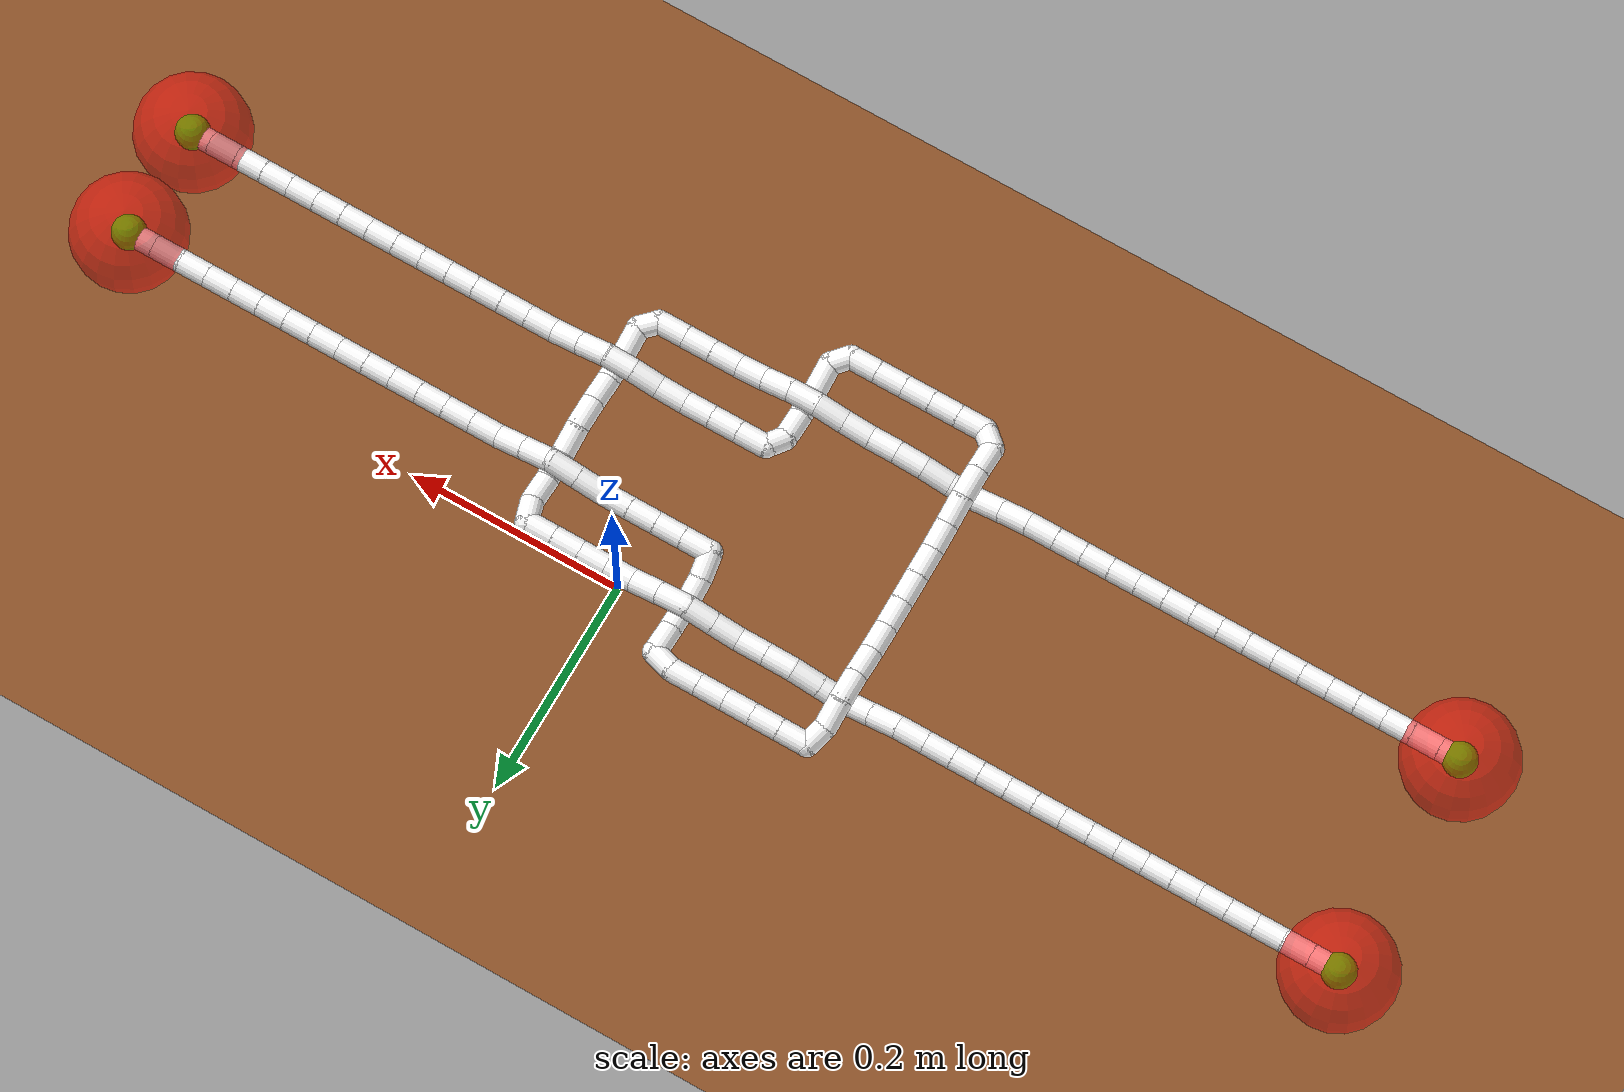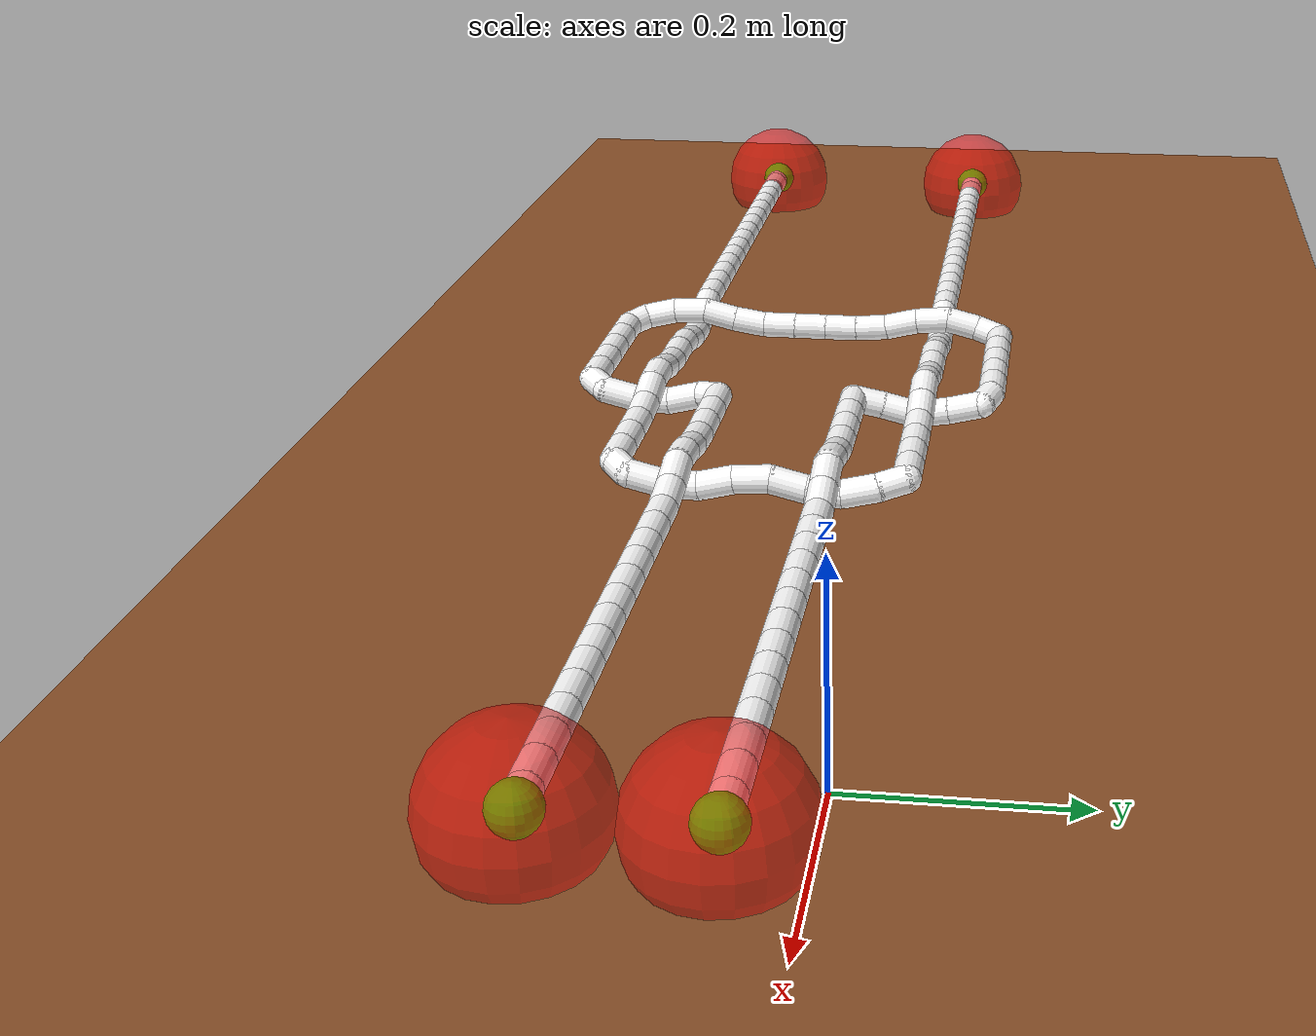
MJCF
<mujoco model="rope_knot">
    <compiler angle="radian" inertiafromgeom="true" />
    <option integrator="Euler" timestep="0.0001" gravity="0 0 -9.81" solver="Newton" iterations="30" tolerance="1e-4">
        <flag contact="enable" />
    </option>

    <visual>
        <global offwidth="1920" offheight="1080" />
        <quality shadowsize="4096" />
        <headlight ambient="0.25 0.25 0.25" diffuse="0.7 0.7 0.7" specular="0.2 0.2 0.2" />
        <rgba haze="0.15 0.15 0.15 1" />
    </visual>

    <asset>
        <!-- 绳子纹理：默认程序纹理；若设置环境变量 ROPE_TEXTURE_FILE，则会用 file=... -->
        <texture name="rope_tex" type="2d" file="../material/Industrial_rope_01.png" />
        <material name="rope_mat" texture="rope_tex" texrepeat="200.0 20.0" texuniform="true"
                  specular="0.06" shininess="0.03" reflectance="0.01" />
    </asset>

    <default>
        <joint damping="0.05" stiffness="0.002" />

        <!-- 绳子碰撞层：只参与物理，不渲染（避免与视觉层叠加导致怪异高光/摩尔纹） -->
        <default class="rope_col">
            <geom type="capsule" mass="0.0020"
                  friction="0.8 0.02 0.001" density="1000"
                  contype="1" conaffinity="1"
                  rgba="0 0 0 0"
                  solref="0.02 1" solimp="0.9 0.95 0.001" />
        </default>

        <!-- 绳子视觉层：只渲染不碰撞/不计质量 -->
        <default class="rope_vis">
            <geom type="capsule" material="rope_mat" rgba="1 1 1 1" contype="0" conaffinity="0" mass="0" />
        </default>
    </default>

    <worldbody>
        <light pos="0 0 1" dir="0 0 -1" directional="true" castshadow="true" />
        <!-- 自动贴合绳子最低点的实体桌面：参与碰撞与摩擦。 -->
        <geom name="table" type="plane" pos="0 0 0.256781"
              size="2 2 0.1" rgba=".55 .32 .16 1"
              friction="0.9 0.02 0.001" contype="2" conaffinity="1"
              solref="0.01 1" solimp="0.95 0.99 0.001" />

        <body name="rope0_mocap_left" mocap="true" pos="0.4485 0.0080 0.2790">
            <geom type="sphere" size="0.05" rgba="1 0 0 0.5"
                  contype="0" conaffinity="0" mass="0" />
        </body>
        <body name="rope0_mocap_right" mocap="true" pos="0.4483 -0.0920 0.2792">
            <geom type="sphere" size="0.05" rgba="1 0 0 0.5"
                  contype="0" conaffinity="0" mass="0" />
        </body>

        <body name="rope1_mocap_left" mocap="true" pos="-0.7012 0.0595 0.2798">
            <geom type="sphere" size="0.05" rgba="1 0 0 0.5"
                  contype="0" conaffinity="0" mass="0" />
        </body>
        <body name="rope1_mocap_right" mocap="true" pos="-0.7015 -0.1404 0.2803">
            <geom type="sphere" size="0.05" rgba="1 0 0 0.5"
                  contype="0" conaffinity="0" mass="0" />
        </body>
		<body name="rope0_seg_000" pos="0.4485 0.0080 0.2790" quat="1.0000 0.0000 0.0000 0.0000">
			<freejoint name="rope0_free_000"/>
			<geom name="rope0_seg_000_col" class="rope_col" type="capsule" fromto="0 0 0 -0.0250 0.0000 0.0000" size="0.0100" />
			<geom name="rope0_seg_000_vis" class="rope_vis" type="capsule" fromto="0 0 0 -0.0250 0.0000 0.0000" size="0.0100" />
			<site name="anchor_rope0_seg_000" pos="0 0 0" size="0.0150" rgba="0 1 0 1" />
			<body name="rope0_seg_001" pos="-0.0250 0.0000 0.0000" quat="1.0000 0.0000 0.0000 0.0000">
				<joint name="rope0_joint_000" type="ball" pos="0 0 0" />
				<geom name="rope0_seg_001_col" class="rope_col" type="capsule" fromto="0 0 0 -0.0250 0.0000 0.0000" size="0.0100" />
				<geom name="rope0_seg_001_vis" class="rope_vis" type="capsule" fromto="0.0005 -0.0000 -0.0000 -0.0250 0.0000 0.0000" size="0.0100" />
				<body name="rope0_seg_002" pos="-0.0250 0.0000 0.0000" quat="1.0000 0.0000 0.0000 0.0000">
					<joint name="rope0_joint_001" type="ball" pos="0 0 0" />
					<geom name="rope0_seg_002_col" class="rope_col" type="capsule" fromto="0 0 0 -0.0250 0.0000 0.0000" size="0.0100" />
					<geom name="rope0_seg_002_vis" class="rope_vis" type="capsule" fromto="0.0005 -0.0000 -0.0000 -0.0250 0.0000 0.0000" size="0.0100" />
					<body name="rope0_seg_003" pos="-0.0250 0.0000 0.0000" quat="1.0000 0.0000 0.0000 0.0000">
						<joint name="rope0_joint_002" type="ball" pos="0 0 0" />
						<geom name="rope0_seg_003_col" class="rope_col" type="capsule" fromto="0 0 0 -0.0250 0.0000 0.0000" size="0.0100" />
						<geom name="rope0_seg_003_vis" class="rope_vis" type="capsule" fromto="0.0005 -0.0000 -0.0000 -0.0250 0.0000 0.0000" size="0.0100" />
						<body name="rope0_seg_004" pos="-0.0250 0.0000 0.0000" quat="1.0000 0.0000 0.0000 0.0000">
							<joint name="rope0_joint_003" type="ball" pos="0 0 0" />
							<geom name="rope0_seg_004_col" class="rope_col" type="capsule" fromto="0 0 0 -0.0250 0.0000 0.0000" size="0.0100" />
							<geom name="rope0_seg_004_vis" class="rope_vis" type="capsule" fromto="0.0005 -0.0000 -0.0000 -0.0250 0.0000 0.0000" size="0.0100" />
							<body name="rope0_seg_005" pos="-0.0250 0.0000 0.0000" quat="1.0000 0.0000 0.0000 0.0000">
								<joint name="rope0_joint_004" type="ball" pos="0 0 0" />
								<geom name="rope0_seg_005_col" class="rope_col" type="capsule" fromto="0 0 0 -0.0250 0.0000 0.0000" size="0.0100" />
								<geom name="rope0_seg_005_vis" class="rope_vis" type="capsule" fromto="0.0005 -0.0000 -0.0000 -0.0250 0.0000 0.0000" size="0.0100" />
								<body name="rope0_seg_006" pos="-0.0250 0.0000 0.0000" quat="1.0000 0.0000 0.0000 0.0000">
									<joint name="rope0_joint_005" type="ball" pos="0 0 0" />
									<geom name="rope0_seg_006_col" class="rope_col" type="capsule" fromto="0 0 0 -0.0250 0.0000 0.0000" size="0.0100" />
									<geom name="rope0_seg_006_vis" class="rope_vis" type="capsule" fromto="0.0005 -0.0000 -0.0000 -0.0250 0.0000 0.0000" size="0.0100" />
									<body name="rope0_seg_007" pos="-0.0250 0.0000 0.0000" quat="1.0000 0.0000 0.0000 0.0000">
										<joint name="rope0_joint_006" type="ball" pos="0 0 0" />
										<geom name="rope0_seg_007_col" class="rope_col" type="capsule" fromto="0 0 0 -0.0250 0.0000 0.0000" size="0.0100" />
										<geom name="rope0_seg_007_vis" class="rope_vis" type="capsule" fromto="0.0005 -0.0000 -0.0000 -0.0250 0.0000 0.0000" size="0.0100" />
										<body name="rope0_seg_008" pos="-0.0250 0.0000 0.0000" quat="1.0000 0.0000 0.0000 0.0000">
											<joint name="rope0_joint_007" type="ball" pos="0 0 0" />
											<geom name="rope0_seg_008_col" class="rope_col" type="capsule" fromto="0 0 0 -0.0250 0.0000 0.0000" size="0.0100" />
											<geom name="rope0_seg_008_vis" class="rope_vis" type="capsule" fromto="0.0005 -0.0000 -0.0000 -0.0250 0.0000 0.0000" size="0.0100" />
											<body name="rope0_seg_009" pos="-0.0250 0.0000 0.0000" quat="1.0000 0.0000 0.0000 0.0000">
												<joint name="rope0_joint_008" type="ball" pos="0 0 0" />
												<geom name="rope0_seg_009_col" class="rope_col" type="capsule" fromto="0 0 0 -0.0250 0.0000 0.0000" size="0.0100" />
												<geom name="rope0_seg_009_vis" class="rope_vis" type="capsule" fromto="0.0005 -0.0000 -0.0000 -0.0250 0.0000 0.0000" size="0.0100" />
												<body name="rope0_seg_010" pos="-0.0250 0.0000 0.0000" quat="1.0000 0.0000 0.0000 0.0000">
													<joint name="rope0_joint_009" type="ball" pos="0 0 0" />
													<geom name="rope0_seg_010_col" class="rope_col" type="capsule" fromto="0 0 0 -0.0250 0.0000 0.0000" size="0.0100" />
													<geom name="rope0_seg_010_vis" class="rope_vis" type="capsule" fromto="0.0005 -0.0000 -0.0000 -0.0250 0.0000 0.0000" size="0.0100" />
													<body name="rope0_seg_011" pos="-0.0250 0.0000 0.0000" quat="1.0000 0.0000 0.0000 0.0000">
														<joint name="rope0_joint_010" type="ball" pos="0 0 0" />
														<geom name="rope0_seg_011_col" class="rope_col" type="capsule" fromto="0 0 0 -0.0250 0.0000 0.0000" size="0.0100" />
														<geom name="rope0_seg_011_vis" class="rope_vis" type="capsule" fromto="0.0005 -0.0000 -0.0000 -0.0250 0.0000 0.0000" size="0.0100" />
														<body name="rope0_seg_012" pos="-0.0250 0.0000 0.0000" quat="1.0000 0.0000 0.0000 0.0000">
															<joint name="rope0_joint_011" type="ball" pos="0 0 0" />
															<geom name="rope0_seg_012_col" class="rope_col" type="capsule" fromto="0 0 0 -0.0250 0.0000 0.0000" size="0.0100" />
															<geom name="rope0_seg_012_vis" class="rope_vis" type="capsule" fromto="0.0005 -0.0000 -0.0000 -0.0250 0.0000 0.0000" size="0.0100" />
															<body name="rope0_seg_013" pos="-0.0250 0.0000 0.0000" quat="1.0000 0.0000 0.0000 0.0000">
																<joint name="rope0_joint_012" type="ball" pos="0 0 0" />
																<geom name="rope0_seg_013_col" class="rope_col" type="capsule" fromto="0 0 0 -0.0250 0.0000 0.0000" size="0.0100" />
																<geom name="rope0_seg_013_vis" class="rope_vis" type="capsule" fromto="0.0005 -0.0000 -0.0000 -0.0250 0.0000 0.0000" size="0.0100" />
																<body name="rope0_seg_014" pos="-0.0250 0.0000 0.0000" quat="1.0000 0.0000 0.0000 0.0000">
																	<joint name="rope0_joint_013" type="ball" pos="0 0 0" />
																	<geom name="rope0_seg_014_col" class="rope_col" type="capsule" fromto="0 0 0 -0.0242 0.0000 0.0061" size="0.0100" />
																	<geom name="rope0_seg_014_vis" class="rope_vis" type="capsule" fromto="0.0005 -0.0000 -0.0001 -0.0242 0.0000 0.0061" size="0.0100" />
																	<body name="rope0_seg_015" pos="-0.0242 0.0000 0.0061" quat="1.0000 0.0000 0.0000 0.0000">
																		<joint name="rope0_joint_014" type="ball" pos="0 0 0" />
																		<geom name="rope0_seg_015_col" class="rope_col" type="capsule" fromto="0 0 0 -0.0242 0.0000 0.0061" size="0.0100" />
																		<geom name="rope0_seg_015_vis" class="rope_vis" type="capsule" fromto="0.0005 -0.0000 -0.0001 -0.0242 0.0000 0.0061" size="0.0100" />
																		<body name="rope0_seg_016" pos="-0.0242 0.0000 0.0061" quat="1.0000 0.0000 0.0000 0.0000">
																			<joint name="rope0_joint_015" type="ball" pos="0 0 0" />
																			<geom name="rope0_seg_016_col" class="rope_col" type="capsule" fromto="0 0 0 -0.0243 0.0000 -0.0053" size="0.0100" />
																			<geom name="rope0_seg_016_vis" class="rope_vis" type="capsule" fromto="0.0005 -0.0000 0.0001 -0.0243 0.0000 -0.0053" size="0.0100" />
																			<body name="rope0_seg_017" pos="-0.0243 0.0000 -0.0053" quat="1.0000 0.0000 0.0000 0.0000">
																				<joint name="rope0_joint_016" type="ball" pos="0 0 0" />
																				<geom name="rope0_seg_017_col" class="rope_col" type="capsule" fromto="0 0 0 -0.0243 0.0000 -0.0060" size="0.0100" />
																				<geom name="rope0_seg_017_vis" class="rope_vis" type="capsule" fromto="0.0005 -0.0000 0.0001 -0.0243 0.0000 -0.0060" size="0.0100" />
																				<body name="rope0_seg_018" pos="-0.0243 0.0000 -0.0060" quat="1.0000 0.0000 0.0000 0.0000">
																					<joint name="rope0_joint_017" type="ball" pos="0 0 0" />
																					<geom name="rope0_seg_018_col" class="rope_col" type="capsule" fromto="0 0 0 -0.0249 0.0000 -0.0007" size="0.0100" />
																					<geom name="rope0_seg_018_vis" class="rope_vis" type="capsule" fromto="0.0005 -0.0000 0.0000 -0.0249 0.0000 -0.0007" size="0.0100" />
																					<body name="rope0_seg_019" pos="-0.0249 0.0000 -0.0007" quat="1.0000 0.0000 0.0000 0.0000">
																						<joint name="rope0_joint_018" type="ball" pos="0 0 0" />
																						<geom name="rope0_seg_019_col" class="rope_col" type="capsule" fromto="0 0 0 -0.0250 0.0000 0.0000" size="0.0100" />
																						<geom name="rope0_seg_019_vis" class="rope_vis" type="capsule" fromto="0.0005 -0.0000 -0.0000 -0.0250 0.0000 0.0000" size="0.0100" />
																						<body name="rope0_seg_020" pos="-0.0250 0.0000 0.0000" quat="1.0000 0.0000 0.0000 0.0000">
																							<joint name="rope0_joint_019" type="ball" pos="0 0 0" />
																							<geom name="rope0_seg_020_col" class="rope_col" type="capsule" fromto="0 0 0 -0.0250 0.0000 0.0000" size="0.0100" />
																							<geom name="rope0_seg_020_vis" class="rope_vis" type="capsule" fromto="0.0005 -0.0000 -0.0000 -0.0250 0.0000 0.0000" size="0.0100" />
																							<body name="rope0_seg_021" pos="-0.0250 0.0000 0.0000" quat="1.0000 0.0000 0.0000 0.0000">
																								<joint name="rope0_joint_020" type="ball" pos="0 0 0" />
																								<geom name="rope0_seg_021_col" class="rope_col" type="capsule" fromto="0 0 0 -0.0250 0.0000 0.0000" size="0.0100" />
																								<geom name="rope0_seg_021_vis" class="rope_vis" type="capsule" fromto="0.0005 -0.0000 -0.0000 -0.0250 0.0000 0.0000" size="0.0100" />
																								<body name="rope0_seg_022" pos="-0.0250 0.0000 0.0000" quat="1.0000 0.0000 0.0000 0.0000">
																									<joint name="rope0_joint_021" type="ball" pos="0 0 0" />
																									<geom name="rope0_seg_022_col" class="rope_col" type="capsule" fromto="0 0 0 -0.0029 0.0214 -0.0054" size="0.0100" />
																									<geom name="rope0_seg_022_vis" class="rope_vis" type="capsule" fromto="0.0001 -0.0004 0.0001 -0.0029 0.0214 -0.0054" size="0.0100" />
																									<body name="rope0_seg_023" pos="-0.0029 0.0214 -0.0054" quat="1.0000 0.0000 0.0000 0.0000">
																										<joint name="rope0_joint_022" type="ball" pos="0 0 0" />
																										<geom name="rope0_seg_023_col" class="rope_col" type="capsule" fromto="0 0 0 0.0000 0.0242 -0.0061" size="0.0100" />
																										<geom name="rope0_seg_023_vis" class="rope_vis" type="capsule" fromto="-0.0000 -0.0005 0.0001 0.0000 0.0242 -0.0061" size="0.0100" />
																										<body name="rope0_seg_024" pos="0.0000 0.0242 -0.0061" quat="1.0000 0.0000 0.0000 0.0000">
																											<joint name="rope0_joint_023" type="ball" pos="0 0 0" />
																											<geom name="rope0_seg_024_col" class="rope_col" type="capsule" fromto="0 0 0 0.0000 0.0243 0.0038" size="0.0100" />
																											<geom name="rope0_seg_024_vis" class="rope_vis" type="capsule" fromto="-0.0000 -0.0005 -0.0001 0.0000 0.0243 0.0038" size="0.0100" />
																											<body name="rope0_seg_025" pos="0.0000 0.0243 0.0038" quat="1.0000 0.0000 0.0000 0.0000">
																												<joint name="rope0_joint_024" type="ball" pos="0 0 0" />
																												<geom name="rope0_seg_025_col" class="rope_col" type="capsule" fromto="0 0 0 0.0000 0.0243 0.0060" size="0.0100" />
																												<geom name="rope0_seg_025_vis" class="rope_vis" type="capsule" fromto="-0.0000 -0.0005 -0.0001 0.0000 0.0243 0.0060" size="0.0100" />
																												<body name="rope0_seg_026" pos="0.0000 0.0243 0.0060" quat="1.0000 0.0000 0.0000 0.0000">
																													<joint name="rope0_joint_025" type="ball" pos="0 0 0" />
																													<geom name="rope0_seg_026_col" class="rope_col" type="capsule" fromto="0 0 0 -0.0190 0.0059 0.0015" size="0.0100" />
																													<geom name="rope0_seg_026_vis" class="rope_vis" type="capsule" fromto="0.0004 -0.0001 -0.0000 -0.0190 0.0059 0.0015" size="0.0100" />
																													<body name="rope0_seg_027" pos="-0.0190 0.0059 0.0015" quat="1.0000 0.0000 0.0000 0.0000">
																														<joint name="rope0_joint_026" type="ball" pos="0 0 0" />
																														<geom name="rope0_seg_027_col" class="rope_col" type="capsule" fromto="0 0 0 -0.0250 0.0000 0.0000" size="0.0100" />
																														<geom name="rope0_seg_027_vis" class="rope_vis" type="capsule" fromto="0.0005 -0.0000 -0.0000 -0.0250 0.0000 0.0000" size="0.0100" />
																														<body name="rope0_seg_028" pos="-0.0250 0.0000 0.0000" quat="1.0000 0.0000 0.0000 0.0000">
																															<joint name="rope0_joint_027" type="ball" pos="0 0 0" />
																															<geom name="rope0_seg_028_col" class="rope_col" type="capsule" fromto="0 0 0 -0.0250 0.0000 0.0000" size="0.0100" />
																															<geom name="rope0_seg_028_vis" class="rope_vis" type="capsule" fromto="0.0005 -0.0000 -0.0000 -0.0250 0.0000 0.0000" size="0.0100" />
																															<body name="rope0_seg_029" pos="-0.0250 0.0000 0.0000" quat="1.0000 0.0000 0.0000 0.0000">
																																<joint name="rope0_joint_028" type="ball" pos="0 0 0" />
																																<geom name="rope0_seg_029_col" class="rope_col" type="capsule" fromto="0 0 0 -0.0250 0.0000 0.0000" size="0.0100" />
																																<geom name="rope0_seg_029_vis" class="rope_vis" type="capsule" fromto="0.0005 -0.0000 -0.0000 -0.0250 0.0000 0.0000" size="0.0100" />
																																<body name="rope0_seg_030" pos="-0.0250 0.0000 0.0000" quat="1.0000 0.0000 0.0000 0.0000">
																																	<joint name="rope0_joint_029" type="ball" pos="0 0 0" />
																																	<geom name="rope0_seg_030_col" class="rope_col" type="capsule" fromto="0 0 0 -0.0250 0.0000 0.0000" size="0.0100" />
																																	<geom name="rope0_seg_030_vis" class="rope_vis" type="capsule" fromto="0.0005 -0.0000 -0.0000 -0.0250 0.0000 0.0000" size="0.0100" />
																																	<body name="rope0_seg_031" pos="-0.0250 0.0000 0.0000" quat="1.0000 0.0000 0.0000 0.0000">
																																		<joint name="rope0_joint_030" type="ball" pos="0 0 0" />
																																		<geom name="rope0_seg_031_col" class="rope_col" type="capsule" fromto="0 0 0 -0.0250 0.0000 0.0000" size="0.0100" />
																																		<geom name="rope0_seg_031_vis" class="rope_vis" type="capsule" fromto="0.0005 -0.0000 -0.0000 -0.0250 0.0000 0.0000" size="0.0100" />
																																		<body name="rope0_seg_032" pos="-0.0250 0.0000 0.0000" quat="1.0000 0.0000 0.0000 0.0000">
																																			<joint name="rope0_joint_031" type="ball" pos="0 0 0" />
																																			<geom name="rope0_seg_032_col" class="rope_col" type="capsule" fromto="0 0 0 -0.0060 -0.0184 0.0047" size="0.0100" />
																																			<geom name="rope0_seg_032_vis" class="rope_vis" type="capsule" fromto="0.0001 0.0004 -0.0001 -0.0060 -0.0184 0.0047" size="0.0100" />
																																			<body name="rope0_seg_033" pos="-0.0060 -0.0184 0.0047" quat="1.0000 0.0000 0.0000 0.0000">
																																				<joint name="rope0_joint_032" type="ball" pos="0 0 0" />
																																				<geom name="rope0_seg_033_col" class="rope_col" type="capsule" fromto="0 0 0 -0.0000 -0.0242 0.0061" size="0.0100" />
																																				<geom name="rope0_seg_033_vis" class="rope_vis" type="capsule" fromto="0.0000 0.0005 -0.0001 -0.0000 -0.0242 0.0061" size="0.0100" />
																																				<body name="rope0_seg_034" pos="-0.0000 -0.0242 0.0061" quat="1.0000 0.0000 0.0000 0.0000">
																																					<joint name="rope0_joint_033" type="ball" pos="0 0 0" />
																																					<geom name="rope0_seg_034_col" class="rope_col" type="capsule" fromto="0 0 0 -0.0000 -0.0243 -0.0024" size="0.0100" />
																																					<geom name="rope0_seg_034_vis" class="rope_vis" type="capsule" fromto="0.0000 0.0005 0.0000 -0.0000 -0.0243 -0.0024" size="0.0100" />
																																					<body name="rope0_seg_035" pos="-0.0000 -0.0243 -0.0024" quat="1.0000 0.0000 0.0000 0.0000">
																																						<joint name="rope0_joint_034" type="ball" pos="0 0 0" />
																																						<geom name="rope0_seg_035_col" class="rope_col" type="capsule" fromto="0 0 0 -0.0000 -0.0243 -0.0060" size="0.0100" />
																																						<geom name="rope0_seg_035_vis" class="rope_vis" type="capsule" fromto="0.0000 0.0005 0.0001 -0.0000 -0.0243 -0.0060" size="0.0100" />
																																						<body name="rope0_seg_036" pos="-0.0000 -0.0243 -0.0060" quat="1.0000 0.0000 0.0000 0.0000">
																																							<joint name="rope0_joint_035" type="ball" pos="0 0 0" />
																																							<geom name="rope0_seg_036_col" class="rope_col" type="capsule" fromto="0 0 0 -0.0000 -0.0247 -0.0021" size="0.0100" />
																																							<geom name="rope0_seg_036_vis" class="rope_vis" type="capsule" fromto="0.0000 0.0005 0.0000 -0.0000 -0.0247 -0.0021" size="0.0100" />
																																							<body name="rope0_seg_037" pos="-0.0000 -0.0247 -0.0021" quat="1.0000 0.0000 0.0000 0.0000">
																																								<joint name="rope0_joint_036" type="ball" pos="0 0 0" />
																																								<geom name="rope0_seg_037_col" class="rope_col" type="capsule" fromto="0 0 0 -0.0000 -0.0250 0.0001" size="0.0100" />
																																								<geom name="rope0_seg_037_vis" class="rope_vis" type="capsule" fromto="0.0000 0.0005 -0.0000 -0.0000 -0.0250 0.0001" size="0.0100" />
																																								<body name="rope0_seg_038" pos="-0.0000 -0.0250 0.0001" quat="1.0000 0.0000 0.0000 0.0000">
																																									<joint name="rope0_joint_037" type="ball" pos="0 0 0" />
																																									<geom name="rope0_seg_038_col" class="rope_col" type="capsule" fromto="0 0 0 -0.0000 -0.0250 0.0001" size="0.0100" />
																																									<geom name="rope0_seg_038_vis" class="rope_vis" type="capsule" fromto="0.0000 0.0005 -0.0000 -0.0000 -0.0250 0.0001" size="0.0100" />
																																									<body name="rope0_seg_039" pos="-0.0000 -0.0250 0.0001" quat="1.0000 0.0000 0.0000 0.0000">
																																										<joint name="rope0_joint_038" type="ball" pos="0 0 0" />
																																										<geom name="rope0_seg_039_col" class="rope_col" type="capsule" fromto="0 0 0 -0.0000 -0.0250 0.0001" size="0.0100" />
																																										<geom name="rope0_seg_039_vis" class="rope_vis" type="capsule" fromto="0.0000 0.0005 -0.0000 -0.0000 -0.0250 0.0001" size="0.0100" />
																																										<body name="rope0_seg_040" pos="-0.0000 -0.0250 0.0001" quat="1.0000 0.0000 0.0000 0.0000">
																																											<joint name="rope0_joint_039" type="ball" pos="0 0 0" />
																																											<geom name="rope0_seg_040_col" class="rope_col" type="capsule" fromto="0 0 0 -0.0000 -0.0245 0.0039" size="0.0100" />
																																											<geom name="rope0_seg_040_vis" class="rope_vis" type="capsule" fromto="0.0000 0.0005 -0.0001 -0.0000 -0.0245 0.0039" size="0.0100" />
																																											<body name="rope0_seg_041" pos="-0.0000 -0.0245 0.0039" quat="1.0000 0.0000 0.0000 0.0000">
																																												<joint name="rope0_joint_040" type="ball" pos="0 0 0" />
																																												<geom name="rope0_seg_041_col" class="rope_col" type="capsule" fromto="0 0 0 -0.0000 -0.0242 0.0061" size="0.0100" />
																																												<geom name="rope0_seg_041_vis" class="rope_vis" type="capsule" fromto="0.0000 0.0005 -0.0001 -0.0000 -0.0242 0.0061" size="0.0100" />
																																												<body name="rope0_seg_042" pos="-0.0000 -0.0242 0.0061" quat="1.0000 0.0000 0.0000 0.0000">
																																													<joint name="rope0_joint_041" type="ball" pos="0 0 0" />
																																													<geom name="rope0_seg_042_col" class="rope_col" type="capsule" fromto="0 0 0 -0.0000 -0.0243 -0.0009" size="0.0100" />
																																													<geom name="rope0_seg_042_vis" class="rope_vis" type="capsule" fromto="0.0000 0.0005 0.0000 -0.0000 -0.0243 -0.0009" size="0.0100" />
																																													<body name="rope0_seg_043" pos="-0.0000 -0.0243 -0.0009" quat="1.0000 0.0000 0.0000 0.0000">
																																														<joint name="rope0_joint_042" type="ball" pos="0 0 0" />
																																														<geom name="rope0_seg_043_col" class="rope_col" type="capsule" fromto="0 0 0 -0.0000 -0.0243 -0.0060" size="0.0100" />
																																														<geom name="rope0_seg_043_vis" class="rope_vis" type="capsule" fromto="0.0000 0.0005 0.0001 -0.0000 -0.0243 -0.0060" size="0.0100" />
																																														<body name="rope0_seg_044" pos="-0.0000 -0.0243 -0.0060" quat="1.0000 0.0000 0.0000 0.0000">
																																															<joint name="rope0_joint_043" type="ball" pos="0 0 0" />
																																															<geom name="rope0_seg_044_col" class="rope_col" type="capsule" fromto="0 0 0 0.0129 -0.0118 -0.0029" size="0.0100" />
																																															<geom name="rope0_seg_044_vis" class="rope_vis" type="capsule" fromto="-0.0003 0.0002 0.0001 0.0129 -0.0118 -0.0029" size="0.0100" />
																																															<body name="rope0_seg_045" pos="0.0129 -0.0118 -0.0029" quat="1.0000 0.0000 0.0000 0.0000">
																																																<joint name="rope0_joint_044" type="ball" pos="0 0 0" />
																																																<geom name="rope0_seg_045_col" class="rope_col" type="capsule" fromto="0 0 0 0.0250 -0.0000 -0.0000" size="0.0100" />
																																																<geom name="rope0_seg_045_vis" class="rope_vis" type="capsule" fromto="-0.0005 0.0000 0.0000 0.0250 -0.0000 -0.0000" size="0.0100" />
																																																<body name="rope0_seg_046" pos="0.0250 -0.0000 -0.0000" quat="1.0000 0.0000 0.0000 0.0000">
																																																	<joint name="rope0_joint_045" type="ball" pos="0 0 0" />
																																																	<geom name="rope0_seg_046_col" class="rope_col" type="capsule" fromto="0 0 0 0.0250 -0.0000 -0.0000" size="0.0100" />
																																																	<geom name="rope0_seg_046_vis" class="rope_vis" type="capsule" fromto="-0.0005 0.0000 0.0000 0.0250 -0.0000 -0.0000" size="0.0100" />
																																																	<body name="rope0_seg_047" pos="0.0250 -0.0000 -0.0000" quat="1.0000 0.0000 0.0000 0.0000">
																																																		<joint name="rope0_joint_046" type="ball" pos="0 0 0" />
																																																		<geom name="rope0_seg_047_col" class="rope_col" type="capsule" fromto="0 0 0 0.0250 -0.0000 -0.0000" size="0.0100" />
																																																		<geom name="rope0_seg_047_vis" class="rope_vis" type="capsule" fromto="-0.0005 0.0000 0.0000 0.0250 -0.0000 -0.0000" size="0.0100" />
																																																		<body name="rope0_seg_048" pos="0.0250 -0.0000 -0.0000" quat="1.0000 0.0000 0.0000 0.0000">
																																																			<joint name="rope0_joint_047" type="ball" pos="0 0 0" />
																																																			<geom name="rope0_seg_048_col" class="rope_col" type="capsule" fromto="0 0 0 0.0250 -0.0000 -0.0000" size="0.0100" />
																																																			<geom name="rope0_seg_048_vis" class="rope_vis" type="capsule" fromto="-0.0005 0.0000 0.0000 0.0250 -0.0000 -0.0000" size="0.0100" />
																																																			<body name="rope0_seg_049" pos="0.0250 -0.0000 -0.0000" quat="1.0000 0.0000 0.0000 0.0000">
																																																				<joint name="rope0_joint_048" type="ball" pos="0 0 0" />
																																																				<geom name="rope0_seg_049_col" class="rope_col" type="capsule" fromto="0 0 0 0.0250 -0.0000 -0.0000" size="0.0100" />
																																																				<geom name="rope0_seg_049_vis" class="rope_vis" type="capsule" fromto="-0.0005 0.0000 0.0000 0.0250 -0.0000 -0.0000" size="0.0100" />
																																																				<body name="rope0_seg_050" pos="0.0250 -0.0000 -0.0000" quat="1.0000 0.0000 0.0000 0.0000">
																																																					<joint name="rope0_joint_049" type="ball" pos="0 0 0" />
																																																					<geom name="rope0_seg_050_col" class="rope_col" type="capsule" fromto="0 0 0 0.0121 0.0125 -0.0032" size="0.0100" />
																																																					<geom name="rope0_seg_050_vis" class="rope_vis" type="capsule" fromto="-0.0002 -0.0003 0.0001 0.0121 0.0125 -0.0032" size="0.0100" />
																																																					<body name="rope0_seg_051" pos="0.0121 0.0125 -0.0032" quat="1.0000 0.0000 0.0000 0.0000">
																																																						<joint name="rope0_joint_050" type="ball" pos="0 0 0" />
																																																						<geom name="rope0_seg_051_col" class="rope_col" type="capsule" fromto="0 0 0 0.0000 0.0242 -0.0061" size="0.0100" />
																																																						<geom name="rope0_seg_051_vis" class="rope_vis" type="capsule" fromto="-0.0000 -0.0005 0.0001 0.0000 0.0242 -0.0061" size="0.0100" />
																																																						<body name="rope0_seg_052" pos="0.0000 0.0242 -0.0061" quat="1.0000 0.0000 0.0000 0.0000">
																																																							<joint name="rope0_joint_051" type="ball" pos="0 0 0" />
																																																							<geom name="rope0_seg_052_col" class="rope_col" type="capsule" fromto="0 0 0 0.0000 0.0243 -0.0006" size="0.0100" />
																																																							<geom name="rope0_seg_052_vis" class="rope_vis" type="capsule" fromto="-0.0000 -0.0005 0.0000 0.0000 0.0243 -0.0006" size="0.0100" />
																																																							<body name="rope0_seg_053" pos="0.0000 0.0243 -0.0006" quat="1.0000 0.0000 0.0000 0.0000">
																																																								<joint name="rope0_joint_052" type="ball" pos="0 0 0" />
																																																								<geom name="rope0_seg_053_col" class="rope_col" type="capsule" fromto="0 0 0 0.0000 0.0243 0.0060" size="0.0100" />
																																																								<geom name="rope0_seg_053_vis" class="rope_vis" type="capsule" fromto="-0.0000 -0.0005 -0.0001 0.0000 0.0243 0.0060" size="0.0100" />
																																																								<body name="rope0_seg_054" pos="0.0000 0.0243 0.0060" quat="1.0000 0.0000 0.0000 0.0000">
																																																									<joint name="rope0_joint_053" type="ball" pos="0 0 0" />
																																																									<geom name="rope0_seg_054_col" class="rope_col" type="capsule" fromto="0 0 0 0.0099 0.0147 0.0036" size="0.0100" />
																																																									<geom name="rope0_seg_054_vis" class="rope_vis" type="capsule" fromto="-0.0002 -0.0003 -0.0001 0.0099 0.0147 0.0036" size="0.0100" />
																																																									<body name="rope0_seg_055" pos="0.0099 0.0147 0.0036" quat="1.0000 0.0000 0.0000 0.0000">
																																																										<joint name="rope0_joint_054" type="ball" pos="0 0 0" />
																																																										<geom name="rope0_seg_055_col" class="rope_col" type="capsule" fromto="0 0 0 0.0250 -0.0000 -0.0000" size="0.0100" />
																																																										<geom name="rope0_seg_055_vis" class="rope_vis" type="capsule" fromto="-0.0005 0.0000 0.0000 0.0250 -0.0000 -0.0000" size="0.0100" />
																																																										<body name="rope0_seg_056" pos="0.0250 -0.0000 -0.0000" quat="1.0000 0.0000 0.0000 0.0000">
																																																											<joint name="rope0_joint_055" type="ball" pos="0 0 0" />
																																																											<geom name="rope0_seg_056_col" class="rope_col" type="capsule" fromto="0 0 0 0.0250 -0.0000 -0.0000" size="0.0100" />
																																																											<geom name="rope0_seg_056_vis" class="rope_vis" type="capsule" fromto="-0.0005 0.0000 0.0000 0.0250 -0.0000 -0.0000" size="0.0100" />
																																																											<body name="rope0_seg_057" pos="0.0250 -0.0000 -0.0000" quat="1.0000 0.0000 0.0000 0.0000">
																																																												<joint name="rope0_joint_056" type="ball" pos="0 0 0" />
																																																												<geom name="rope0_seg_057_col" class="rope_col" type="capsule" fromto="0 0 0 0.0250 -0.0000 -0.0000" size="0.0100" />
																																																												<geom name="rope0_seg_057_vis" class="rope_vis" type="capsule" fromto="-0.0005 0.0000 0.0000 0.0250 -0.0000 -0.0000" size="0.0100" />
																																																												<body name="rope0_seg_058" pos="0.0250 -0.0000 -0.0000" quat="1.0000 0.0000 0.0000 0.0000">
																																																													<joint name="rope0_joint_057" type="ball" pos="0 0 0" />
																																																													<geom name="rope0_seg_058_col" class="rope_col" type="capsule" fromto="0 0 0 0.0247 -0.0000 0.0024" size="0.0100" />
																																																													<geom name="rope0_seg_058_vis" class="rope_vis" type="capsule" fromto="-0.0005 0.0000 -0.0000 0.0247 -0.0000 0.0024" size="0.0100" />
																																																													<body name="rope0_seg_059" pos="0.0247 -0.0000 0.0024" quat="1.0000 0.0000 0.0000 0.0000">
																																																														<joint name="rope0_joint_058" type="ball" pos="0 0 0" />
																																																														<geom name="rope0_seg_059_col" class="rope_col" type="capsule" fromto="0 0 0 0.0243 -0.0000 0.0060" size="0.0100" />
																																																														<geom name="rope0_seg_059_vis" class="rope_vis" type="capsule" fromto="-0.0005 0.0000 -0.0001 0.0243 -0.0000 0.0060" size="0.0100" />
																																																														<body name="rope0_seg_060" pos="0.0243 -0.0000 0.0060" quat="1.0000 0.0000 0.0000 0.0000">
																																																															<joint name="rope0_joint_059" type="ball" pos="0 0 0" />
																																																															<geom name="rope0_seg_060_col" class="rope_col" type="capsule" fromto="0 0 0 0.0243 -0.0000 0.0020" size="0.0100" />
																																																															<geom name="rope0_seg_060_vis" class="rope_vis" type="capsule" fromto="-0.0005 0.0000 -0.0000 0.0243 -0.0000 0.0020" size="0.0100" />
																																																															<body name="rope0_seg_061" pos="0.0243 -0.0000 0.0020" quat="1.0000 0.0000 0.0000 0.0000">
																																																																<joint name="rope0_joint_060" type="ball" pos="0 0 0" />
																																																																<geom name="rope0_seg_061_col" class="rope_col" type="capsule" fromto="0 0 0 0.0242 -0.0000 -0.0061" size="0.0100" />
																																																																<geom name="rope0_seg_061_vis" class="rope_vis" type="capsule" fromto="-0.0005 0.0000 0.0001 0.0242 -0.0000 -0.0061" size="0.0100" />
																																																																<body name="rope0_seg_062" pos="0.0242 -0.0000 -0.0061" quat="1.0000 0.0000 0.0000 0.0000">
																																																																	<joint name="rope0_joint_061" type="ball" pos="0 0 0" />
																																																																	<geom name="rope0_seg_062_col" class="rope_col" type="capsule" fromto="0 0 0 0.0245 -0.0000 -0.0044" size="0.0100" />
																																																																	<geom name="rope0_seg_062_vis" class="rope_vis" type="capsule" fromto="-0.0005 0.0000 0.0001 0.0245 -0.0000 -0.0044" size="0.0100" />
																																																																	<body name="rope0_seg_063" pos="0.0245 -0.0000 -0.0044" quat="1.0000 0.0000 0.0000 0.0000">
																																																																		<joint name="rope0_joint_062" type="ball" pos="0 0 0" />
																																																																		<geom name="rope0_seg_063_col" class="rope_col" type="capsule" fromto="0 0 0 0.0250 -0.0000 -0.0000" size="0.0100" />
																																																																		<geom name="rope0_seg_063_vis" class="rope_vis" type="capsule" fromto="-0.0005 0.0000 0.0000 0.0250 -0.0000 -0.0000" size="0.0100" />
																																																																		<body name="rope0_seg_064" pos="0.0250 -0.0000 -0.0000" quat="1.0000 0.0000 0.0000 0.0000">
																																																																			<joint name="rope0_joint_063" type="ball" pos="0 0 0" />
																																																																			<geom name="rope0_seg_064_col" class="rope_col" type="capsule" fromto="0 0 0 0.0250 -0.0000 -0.0000" size="0.0100" />
																																																																			<geom name="rope0_seg_064_vis" class="rope_vis" type="capsule" fromto="-0.0005 0.0000 0.0000 0.0250 -0.0000 -0.0000" size="0.0100" />
																																																																			<body name="rope0_seg_065" pos="0.0250 -0.0000 -0.0000" quat="1.0000 0.0000 0.0000 0.0000">
																																																																				<joint name="rope0_joint_064" type="ball" pos="0 0 0" />
																																																																				<geom name="rope0_seg_065_col" class="rope_col" type="capsule" fromto="0 0 0 0.0250 -0.0000 -0.0000" size="0.0100" />
																																																																				<geom name="rope0_seg_065_vis" class="rope_vis" type="capsule" fromto="-0.0005 0.0000 0.0000 0.0250 -0.0000 -0.0000" size="0.0100" />
																																																																				<body name="rope0_seg_066" pos="0.0250 -0.0000 -0.0000" quat="1.0000 0.0000 0.0000 0.0000">
																																																																					<joint name="rope0_joint_065" type="ball" pos="0 0 0" />
																																																																					<geom name="rope0_seg_066_col" class="rope_col" type="capsule" fromto="0 0 0 0.0250 -0.0000 -0.0000" size="0.0100" />
																																																																					<geom name="rope0_seg_066_vis" class="rope_vis" type="capsule" fromto="-0.0005 0.0000 0.0000 0.0250 -0.0000 -0.0000" size="0.0100" />
																																																																					<body name="rope0_seg_067" pos="0.0250 -0.0000 -0.0000" quat="1.0000 0.0000 0.0000 0.0000">
																																																																						<joint name="rope0_joint_066" type="ball" pos="0 0 0" />
																																																																						<geom name="rope0_seg_067_col" class="rope_col" type="capsule" fromto="0 0 0 0.0250 -0.0000 -0.0000" size="0.0100" />
																																																																						<geom name="rope0_seg_067_vis" class="rope_vis" type="capsule" fromto="-0.0005 0.0000 0.0000 0.0250 -0.0000 -0.0000" size="0.0100" />
																																																																						<body name="rope0_seg_068" pos="0.0250 -0.0000 -0.0000" quat="1.0000 0.0000 0.0000 0.0000">
																																																																							<joint name="rope0_joint_067" type="ball" pos="0 0 0" />
																																																																							<geom name="rope0_seg_068_col" class="rope_col" type="capsule" fromto="0 0 0 0.0250 -0.0000 -0.0000" size="0.0100" />
																																																																							<geom name="rope0_seg_068_vis" class="rope_vis" type="capsule" fromto="-0.0005 0.0000 0.0000 0.0250 -0.0000 -0.0000" size="0.0100" />
																																																																							<body name="rope0_seg_069" pos="0.0250 -0.0000 -0.0000" quat="1.0000 0.0000 0.0000 0.0000">
																																																																								<joint name="rope0_joint_068" type="ball" pos="0 0 0" />
																																																																								<geom name="rope0_seg_069_col" class="rope_col" type="capsule" fromto="0 0 0 0.0250 -0.0000 -0.0000" size="0.0100" />
																																																																								<geom name="rope0_seg_069_vis" class="rope_vis" type="capsule" fromto="-0.0005 0.0000 0.0000 0.0250 -0.0000 -0.0000" size="0.0100" />
																																																																								<body name="rope0_seg_070" pos="0.0250 -0.0000 -0.0000" quat="1.0000 0.0000 0.0000 0.0000">
																																																																									<joint name="rope0_joint_069" type="ball" pos="0 0 0" />
																																																																									<geom name="rope0_seg_070_col" class="rope_col" type="capsule" fromto="0 0 0 0.0250 -0.0000 -0.0000" size="0.0100" />
																																																																									<geom name="rope0_seg_070_vis" class="rope_vis" type="capsule" fromto="-0.0005 0.0000 0.0000 0.0250 -0.0000 -0.0000" size="0.0100" />
																																																																									<body name="rope0_seg_071" pos="0.0250 -0.0000 -0.0000" quat="1.0000 0.0000 0.0000 0.0000">
																																																																										<joint name="rope0_joint_070" type="ball" pos="0 0 0" />
																																																																										<geom name="rope0_seg_071_col" class="rope_col" type="capsule" fromto="0 0 0 0.0250 -0.0000 -0.0000" size="0.0100" />
																																																																										<geom name="rope0_seg_071_vis" class="rope_vis" type="capsule" fromto="-0.0005 0.0000 0.0000 0.0250 -0.0000 -0.0000" size="0.0100" />
																																																																										<body name="rope0_seg_072" pos="0.0250 -0.0000 -0.0000" quat="1.0000 0.0000 0.0000 0.0000">
																																																																											<joint name="rope0_joint_071" type="ball" pos="0 0 0" />
																																																																											<geom name="rope0_seg_072_col" class="rope_col" type="capsule" fromto="0 0 0 0.0250 -0.0000 -0.0000" size="0.0100" />
																																																																											<geom name="rope0_seg_072_vis" class="rope_vis" type="capsule" fromto="-0.0005 0.0000 0.0000 0.0250 -0.0000 -0.0000" size="0.0100" />
																																																																											<body name="rope0_seg_073" pos="0.0250 -0.0000 -0.0000" quat="1.0000 0.0000 0.0000 0.0000">
																																																																												<joint name="rope0_joint_072" type="ball" pos="0 0 0" />
																																																																												<geom name="rope0_seg_073_col" class="rope_col" type="capsule" fromto="0 0 0 0.0250 -0.0000 -0.0000" size="0.0100" />
																																																																												<geom name="rope0_seg_073_vis" class="rope_vis" type="capsule" fromto="-0.0005 0.0000 0.0000 0.0250 -0.0000 -0.0000" size="0.0100" />
																																																																												<body name="rope0_seg_074" pos="0.0250 -0.0000 -0.0000" quat="1.0000 0.0000 0.0000 0.0000">
																																																																													<joint name="rope0_joint_073" type="ball" pos="0 0 0" />
																																																																													<geom name="rope0_seg_074_col" class="rope_col" type="capsule" fromto="0 0 0 0.0250 -0.0000 -0.0000" size="0.0100" />
																																																																													<geom name="rope0_seg_074_vis" class="rope_vis" type="capsule" fromto="-0.0005 0.0000 0.0000 0.0250 -0.0000 -0.0000" size="0.0100" />
																																																																													<body name="rope0_seg_075" pos="0.0250 -0.0000 -0.0000" quat="1.0000 0.0000 0.0000 0.0000">
																																																																														<joint name="rope0_joint_074" type="ball" pos="0 0 0" />
																																																																														<geom name="rope0_seg_075_col" class="rope_col" type="capsule" fromto="0 0 0 0.0250 -0.0000 -0.0000" size="0.0100" />
																																																																														<geom name="rope0_seg_075_vis" class="rope_vis" type="capsule" fromto="-0.0005 0.0000 0.0000 0.0250 -0.0000 -0.0000" size="0.0100" />
																																																																														<body name="rope0_seg_076" pos="0.0250 -0.0000 -0.0000" quat="1.0000 0.0000 0.0000 0.0000">
																																																																															<joint name="rope0_joint_075" type="ball" pos="0 0 0" />
																																																																															<geom name="rope0_seg_076_col" class="rope_col" type="capsule" fromto="0 0 0 0.0181 -0.0000 -0.0000" size="0.0100" />
																																																																															<geom name="rope0_seg_076_vis" class="rope_vis" type="capsule" fromto="-0.0004 0.0000 0.0000 0.0181 -0.0000 -0.0000" size="0.0100" />
																																																																															<body name="rope0_seg_077" pos="0.0181 -0.0000 -0.0000" quat="1.0000 0.0000 0.0000 0.0000">
																																																																																<joint name="rope0_joint_076" type="ball" pos="0 0 0" />
																																																																																<geom name="rope0_seg_077_col" class="rope_col" type="sphere" size="0.0100" />
																																																																																<geom name="rope0_seg_077_vis" class="rope_vis" type="sphere" size="0.0100" />
																																																																																<site name="anchor_rope0_seg_077" pos="0 0 0" size="0.0150" rgba="0 1 0 1" />
																																																																															</body>
																																																																														</body>
																																																																													</body>
																																																																												</body>
																																																																											</body>
																																																																										</body>
																																																																									</body>
																																																																								</body>
																																																																							</body>
																																																																						</body>
																																																																					</body>
																																																																				</body>
																																																																			</body>
																																																																		</body>
																																																																	</body>
																																																																</body>
																																																															</body>
																																																														</body>
																																																													</body>
																																																												</body>
																																																											</body>
																																																										</body>
																																																									</body>
																																																								</body>
																																																							</body>
																																																						</body>
																																																					</body>
																																																				</body>
																																																			</body>
																																																		</body>
																																																	</body>
																																																</body>
																																															</body>
																																														</body>
																																													</body>
																																												</body>
																																											</body>
																																										</body>
																																									</body>
																																								</body>
																																							</body>
																																						</body>
																																					</body>
																																				</body>
																																			</body>
																																		</body>
																																	</body>
																																</body>
																															</body>
																														</body>
																													</body>
																												</body>
																											</body>
																										</body>
																									</body>
																								</body>
																							</body>
																						</body>
																					</body>
																				</body>
																			</body>
																		</body>
																	</body>
																</body>
															</body>
														</body>
													</body>
												</body>
											</body>
										</body>
									</body>
								</body>
							</body>
						</body>
					</body>
				</body>
			</body>
		</body>
		<body name="rope1_seg_000" pos="-0.7012 0.0595 0.2798" quat="1.0000 0.0000 0.0000 0.0000">
			<freejoint name="rope1_free_000"/>
			<geom name="rope1_seg_000_col" class="rope_col" type="capsule" fromto="0 0 0 0.0250 -0.0000 -0.0000" size="0.0100" />
			<geom name="rope1_seg_000_vis" class="rope_vis" type="capsule" fromto="0 0 0 0.0250 -0.0000 -0.0000" size="0.0100" />
			<site name="anchor_rope1_seg_000" pos="0 0 0" size="0.0150" rgba="0 1 0 1" />
			<body name="rope1_seg_001" pos="0.0250 -0.0000 -0.0000" quat="1.0000 0.0000 0.0000 0.0000">
				<joint name="rope1_joint_000" type="ball" pos="0 0 0" />
				<geom name="rope1_seg_001_col" class="rope_col" type="capsule" fromto="0 0 0 0.0250 -0.0000 -0.0000" size="0.0100" />
				<geom name="rope1_seg_001_vis" class="rope_vis" type="capsule" fromto="-0.0005 0.0000 0.0000 0.0250 -0.0000 -0.0000" size="0.0100" />
				<body name="rope1_seg_002" pos="0.0250 -0.0000 -0.0000" quat="1.0000 0.0000 0.0000 0.0000">
					<joint name="rope1_joint_001" type="ball" pos="0 0 0" />
					<geom name="rope1_seg_002_col" class="rope_col" type="capsule" fromto="0 0 0 0.0250 -0.0000 -0.0000" size="0.0100" />
					<geom name="rope1_seg_002_vis" class="rope_vis" type="capsule" fromto="-0.0005 0.0000 0.0000 0.0250 -0.0000 -0.0000" size="0.0100" />
					<body name="rope1_seg_003" pos="0.0250 -0.0000 -0.0000" quat="1.0000 0.0000 0.0000 0.0000">
						<joint name="rope1_joint_002" type="ball" pos="0 0 0" />
						<geom name="rope1_seg_003_col" class="rope_col" type="capsule" fromto="0 0 0 0.0250 -0.0000 -0.0000" size="0.0100" />
						<geom name="rope1_seg_003_vis" class="rope_vis" type="capsule" fromto="-0.0005 0.0000 0.0000 0.0250 -0.0000 -0.0000" size="0.0100" />
						<body name="rope1_seg_004" pos="0.0250 -0.0000 -0.0000" quat="1.0000 0.0000 0.0000 0.0000">
							<joint name="rope1_joint_003" type="ball" pos="0 0 0" />
							<geom name="rope1_seg_004_col" class="rope_col" type="capsule" fromto="0 0 0 0.0250 -0.0000 -0.0000" size="0.0100" />
							<geom name="rope1_seg_004_vis" class="rope_vis" type="capsule" fromto="-0.0005 0.0000 0.0000 0.0250 -0.0000 -0.0000" size="0.0100" />
							<body name="rope1_seg_005" pos="0.0250 -0.0000 -0.0000" quat="1.0000 0.0000 0.0000 0.0000">
								<joint name="rope1_joint_004" type="ball" pos="0 0 0" />
								<geom name="rope1_seg_005_col" class="rope_col" type="capsule" fromto="0 0 0 0.0250 -0.0000 -0.0000" size="0.0100" />
								<geom name="rope1_seg_005_vis" class="rope_vis" type="capsule" fromto="-0.0005 0.0000 0.0000 0.0250 -0.0000 -0.0000" size="0.0100" />
								<body name="rope1_seg_006" pos="0.0250 -0.0000 -0.0000" quat="1.0000 0.0000 0.0000 0.0000">
									<joint name="rope1_joint_005" type="ball" pos="0 0 0" />
									<geom name="rope1_seg_006_col" class="rope_col" type="capsule" fromto="0 0 0 0.0250 -0.0000 -0.0000" size="0.0100" />
									<geom name="rope1_seg_006_vis" class="rope_vis" type="capsule" fromto="-0.0005 0.0000 0.0000 0.0250 -0.0000 -0.0000" size="0.0100" />
									<body name="rope1_seg_007" pos="0.0250 -0.0000 -0.0000" quat="1.0000 0.0000 0.0000 0.0000">
										<joint name="rope1_joint_006" type="ball" pos="0 0 0" />
										<geom name="rope1_seg_007_col" class="rope_col" type="capsule" fromto="0 0 0 0.0250 -0.0000 -0.0000" size="0.0100" />
										<geom name="rope1_seg_007_vis" class="rope_vis" type="capsule" fromto="-0.0005 0.0000 0.0000 0.0250 -0.0000 -0.0000" size="0.0100" />
										<body name="rope1_seg_008" pos="0.0250 -0.0000 -0.0000" quat="1.0000 0.0000 0.0000 0.0000">
											<joint name="rope1_joint_007" type="ball" pos="0 0 0" />
											<geom name="rope1_seg_008_col" class="rope_col" type="capsule" fromto="0 0 0 0.0250 -0.0000 -0.0000" size="0.0100" />
											<geom name="rope1_seg_008_vis" class="rope_vis" type="capsule" fromto="-0.0005 0.0000 0.0000 0.0250 -0.0000 -0.0000" size="0.0100" />
											<body name="rope1_seg_009" pos="0.0250 -0.0000 -0.0000" quat="1.0000 0.0000 0.0000 0.0000">
												<joint name="rope1_joint_008" type="ball" pos="0 0 0" />
												<geom name="rope1_seg_009_col" class="rope_col" type="capsule" fromto="0 0 0 0.0250 -0.0000 -0.0000" size="0.0100" />
												<geom name="rope1_seg_009_vis" class="rope_vis" type="capsule" fromto="-0.0005 0.0000 0.0000 0.0250 -0.0000 -0.0000" size="0.0100" />
												<body name="rope1_seg_010" pos="0.0250 -0.0000 -0.0000" quat="1.0000 0.0000 0.0000 0.0000">
													<joint name="rope1_joint_009" type="ball" pos="0 0 0" />
													<geom name="rope1_seg_010_col" class="rope_col" type="capsule" fromto="0 0 0 0.0250 -0.0000 -0.0000" size="0.0100" />
													<geom name="rope1_seg_010_vis" class="rope_vis" type="capsule" fromto="-0.0005 0.0000 0.0000 0.0250 -0.0000 -0.0000" size="0.0100" />
													<body name="rope1_seg_011" pos="0.0250 -0.0000 -0.0000" quat="1.0000 0.0000 0.0000 0.0000">
														<joint name="rope1_joint_010" type="ball" pos="0 0 0" />
														<geom name="rope1_seg_011_col" class="rope_col" type="capsule" fromto="0 0 0 0.0250 -0.0000 -0.0000" size="0.0100" />
														<geom name="rope1_seg_011_vis" class="rope_vis" type="capsule" fromto="-0.0005 0.0000 0.0000 0.0250 -0.0000 -0.0000" size="0.0100" />
														<body name="rope1_seg_012" pos="0.0250 -0.0000 -0.0000" quat="1.0000 0.0000 0.0000 0.0000">
															<joint name="rope1_joint_011" type="ball" pos="0 0 0" />
															<geom name="rope1_seg_012_col" class="rope_col" type="capsule" fromto="0 0 0 0.0250 -0.0000 -0.0000" size="0.0100" />
															<geom name="rope1_seg_012_vis" class="rope_vis" type="capsule" fromto="-0.0005 0.0000 0.0000 0.0250 -0.0000 -0.0000" size="0.0100" />
															<body name="rope1_seg_013" pos="0.0250 -0.0000 -0.0000" quat="1.0000 0.0000 0.0000 0.0000">
																<joint name="rope1_joint_012" type="ball" pos="0 0 0" />
																<geom name="rope1_seg_013_col" class="rope_col" type="capsule" fromto="0 0 0 0.0250 -0.0000 -0.0000" size="0.0100" />
																<geom name="rope1_seg_013_vis" class="rope_vis" type="capsule" fromto="-0.0005 0.0000 0.0000 0.0250 -0.0000 -0.0000" size="0.0100" />
																<body name="rope1_seg_014" pos="0.0250 -0.0000 -0.0000" quat="1.0000 0.0000 0.0000 0.0000">
																	<joint name="rope1_joint_013" type="ball" pos="0 0 0" />
																	<geom name="rope1_seg_014_col" class="rope_col" type="capsule" fromto="0 0 0 0.0250 -0.0000 -0.0000" size="0.0100" />
																	<geom name="rope1_seg_014_vis" class="rope_vis" type="capsule" fromto="-0.0005 0.0000 0.0000 0.0250 -0.0000 -0.0000" size="0.0100" />
																	<body name="rope1_seg_015" pos="0.0250 -0.0000 -0.0000" quat="1.0000 0.0000 0.0000 0.0000">
																		<joint name="rope1_joint_014" type="ball" pos="0 0 0" />
																		<geom name="rope1_seg_015_col" class="rope_col" type="capsule" fromto="0 0 0 0.0250 -0.0000 -0.0000" size="0.0100" />
																		<geom name="rope1_seg_015_vis" class="rope_vis" type="capsule" fromto="-0.0005 0.0000 0.0000 0.0250 -0.0000 -0.0000" size="0.0100" />
																		<body name="rope1_seg_016" pos="0.0250 -0.0000 -0.0000" quat="1.0000 0.0000 0.0000 0.0000">
																			<joint name="rope1_joint_015" type="ball" pos="0 0 0" />
																			<geom name="rope1_seg_016_col" class="rope_col" type="capsule" fromto="0 0 0 0.0242 -0.0000 -0.0061" size="0.0100" />
																			<geom name="rope1_seg_016_vis" class="rope_vis" type="capsule" fromto="-0.0005 0.0000 0.0001 0.0242 -0.0000 -0.0061" size="0.0100" />
																			<body name="rope1_seg_017" pos="0.0242 -0.0000 -0.0061" quat="1.0000 0.0000 0.0000 0.0000">
																				<joint name="rope1_joint_016" type="ball" pos="0 0 0" />
																				<geom name="rope1_seg_017_col" class="rope_col" type="capsule" fromto="0 0 0 0.0242 -0.0000 -0.0061" size="0.0100" />
																				<geom name="rope1_seg_017_vis" class="rope_vis" type="capsule" fromto="-0.0005 0.0000 0.0001 0.0242 -0.0000 -0.0061" size="0.0100" />
																				<body name="rope1_seg_018" pos="0.0242 -0.0000 -0.0061" quat="1.0000 0.0000 0.0000 0.0000">
																					<joint name="rope1_joint_017" type="ball" pos="0 0 0" />
																					<geom name="rope1_seg_018_col" class="rope_col" type="capsule" fromto="0 0 0 0.0243 -0.0000 0.0053" size="0.0100" />
																					<geom name="rope1_seg_018_vis" class="rope_vis" type="capsule" fromto="-0.0005 0.0000 -0.0001 0.0243 -0.0000 0.0053" size="0.0100" />
																					<body name="rope1_seg_019" pos="0.0243 -0.0000 0.0053" quat="1.0000 0.0000 0.0000 0.0000">
																						<joint name="rope1_joint_018" type="ball" pos="0 0 0" />
																						<geom name="rope1_seg_019_col" class="rope_col" type="capsule" fromto="0 0 0 0.0243 -0.0000 0.0060" size="0.0100" />
																						<geom name="rope1_seg_019_vis" class="rope_vis" type="capsule" fromto="-0.0005 0.0000 -0.0001 0.0243 -0.0000 0.0060" size="0.0100" />
																						<body name="rope1_seg_020" pos="0.0243 -0.0000 0.0060" quat="1.0000 0.0000 0.0000 0.0000">
																							<joint name="rope1_joint_019" type="ball" pos="0 0 0" />
																							<geom name="rope1_seg_020_col" class="rope_col" type="capsule" fromto="0 0 0 0.0249 -0.0000 0.0007" size="0.0100" />
																							<geom name="rope1_seg_020_vis" class="rope_vis" type="capsule" fromto="-0.0005 0.0000 -0.0000 0.0249 -0.0000 0.0007" size="0.0100" />
																							<body name="rope1_seg_021" pos="0.0249 -0.0000 0.0007" quat="1.0000 0.0000 0.0000 0.0000">
																								<joint name="rope1_joint_020" type="ball" pos="0 0 0" />
																								<geom name="rope1_seg_021_col" class="rope_col" type="capsule" fromto="0 0 0 0.0250 -0.0000 -0.0000" size="0.0100" />
																								<geom name="rope1_seg_021_vis" class="rope_vis" type="capsule" fromto="-0.0005 0.0000 0.0000 0.0250 -0.0000 -0.0000" size="0.0100" />
																								<body name="rope1_seg_022" pos="0.0250 -0.0000 -0.0000" quat="1.0000 0.0000 0.0000 0.0000">
																									<joint name="rope1_joint_021" type="ball" pos="0 0 0" />
																									<geom name="rope1_seg_022_col" class="rope_col" type="capsule" fromto="0 0 0 0.0243 -0.0000 0.0053" size="0.0100" />
																									<geom name="rope1_seg_022_vis" class="rope_vis" type="capsule" fromto="-0.0005 0.0000 -0.0001 0.0243 -0.0000 0.0053" size="0.0100" />
																									<body name="rope1_seg_023" pos="0.0243 -0.0000 0.0053" quat="1.0000 0.0000 0.0000 0.0000">
																										<joint name="rope1_joint_022" type="ball" pos="0 0 0" />
																										<geom name="rope1_seg_023_col" class="rope_col" type="capsule" fromto="0 0 0 0.0243 -0.0000 0.0060" size="0.0100" />
																										<geom name="rope1_seg_023_vis" class="rope_vis" type="capsule" fromto="-0.0005 0.0000 -0.0001 0.0243 -0.0000 0.0060" size="0.0100" />
																										<body name="rope1_seg_024" pos="0.0243 -0.0000 0.0060" quat="1.0000 0.0000 0.0000 0.0000">
																											<joint name="rope1_joint_023" type="ball" pos="0 0 0" />
																											<geom name="rope1_seg_024_col" class="rope_col" type="capsule" fromto="0 0 0 0.0243 -0.0000 -0.0039" size="0.0100" />
																											<geom name="rope1_seg_024_vis" class="rope_vis" type="capsule" fromto="-0.0005 0.0000 0.0001 0.0243 -0.0000 -0.0039" size="0.0100" />
																											<body name="rope1_seg_025" pos="0.0243 -0.0000 -0.0039" quat="1.0000 0.0000 0.0000 0.0000">
																												<joint name="rope1_joint_024" type="ball" pos="0 0 0" />
																												<geom name="rope1_seg_025_col" class="rope_col" type="capsule" fromto="0 0 0 0.0242 -0.0000 -0.0061" size="0.0100" />
																												<geom name="rope1_seg_025_vis" class="rope_vis" type="capsule" fromto="-0.0005 0.0000 0.0001 0.0242 -0.0000 -0.0061" size="0.0100" />
																												<body name="rope1_seg_026" pos="0.0242 -0.0000 -0.0061" quat="1.0000 0.0000 0.0000 0.0000">
																													<joint name="rope1_joint_025" type="ball" pos="0 0 0" />
																													<geom name="rope1_seg_026_col" class="rope_col" type="capsule" fromto="0 0 0 0.0248 -0.0000 -0.0015" size="0.0100" />
																													<geom name="rope1_seg_026_vis" class="rope_vis" type="capsule" fromto="-0.0005 0.0000 0.0000 0.0248 -0.0000 -0.0015" size="0.0100" />
																													<body name="rope1_seg_027" pos="0.0248 -0.0000 -0.0015" quat="1.0000 0.0000 0.0000 0.0000">
																														<joint name="rope1_joint_026" type="ball" pos="0 0 0" />
																														<geom name="rope1_seg_027_col" class="rope_col" type="capsule" fromto="0 0 0 0.0250 -0.0000 -0.0000" size="0.0100" />
																														<geom name="rope1_seg_027_vis" class="rope_vis" type="capsule" fromto="-0.0005 0.0000 0.0000 0.0250 -0.0000 -0.0000" size="0.0100" />
																														<body name="rope1_seg_028" pos="0.0250 -0.0000 -0.0000" quat="1.0000 0.0000 0.0000 0.0000">
																															<joint name="rope1_joint_027" type="ball" pos="0 0 0" />
																															<geom name="rope1_seg_028_col" class="rope_col" type="capsule" fromto="0 0 0 0.0250 -0.0000 -0.0000" size="0.0100" />
																															<geom name="rope1_seg_028_vis" class="rope_vis" type="capsule" fromto="-0.0005 0.0000 0.0000 0.0250 -0.0000 -0.0000" size="0.0100" />
																															<body name="rope1_seg_029" pos="0.0250 -0.0000 -0.0000" quat="1.0000 0.0000 0.0000 0.0000">
																																<joint name="rope1_joint_028" type="ball" pos="0 0 0" />
																																<geom name="rope1_seg_029_col" class="rope_col" type="capsule" fromto="0 0 0 0.0250 -0.0000 -0.0000" size="0.0100" />
																																<geom name="rope1_seg_029_vis" class="rope_vis" type="capsule" fromto="-0.0005 0.0000 0.0000 0.0250 -0.0000 -0.0000" size="0.0100" />
																																<body name="rope1_seg_030" pos="0.0250 -0.0000 -0.0000" quat="1.0000 0.0000 0.0000 0.0000">
																																	<joint name="rope1_joint_029" type="ball" pos="0 0 0" />
																																	<geom name="rope1_seg_030_col" class="rope_col" type="capsule" fromto="0 0 0 0.0060 -0.0184 -0.0046" size="0.0100" />
																																	<geom name="rope1_seg_030_vis" class="rope_vis" type="capsule" fromto="-0.0001 0.0004 0.0001 0.0060 -0.0184 -0.0046" size="0.0100" />
																																	<body name="rope1_seg_031" pos="0.0060 -0.0184 -0.0046" quat="1.0000 0.0000 0.0000 0.0000">
																																		<joint name="rope1_joint_030" type="ball" pos="0 0 0" />
																																		<geom name="rope1_seg_031_col" class="rope_col" type="capsule" fromto="0 0 0 -0.0000 -0.0243 -0.0060" size="0.0100" />
																																		<geom name="rope1_seg_031_vis" class="rope_vis" type="capsule" fromto="0.0000 0.0005 0.0001 -0.0000 -0.0243 -0.0060" size="0.0100" />
																																		<body name="rope1_seg_032" pos="-0.0000 -0.0243 -0.0060" quat="1.0000 0.0000 0.0000 0.0000">
																																			<joint name="rope1_joint_031" type="ball" pos="0 0 0" />
																																			<geom name="rope1_seg_032_col" class="rope_col" type="capsule" fromto="0 0 0 -0.0000 -0.0242 0.0025" size="0.0100" />
																																			<geom name="rope1_seg_032_vis" class="rope_vis" type="capsule" fromto="0.0000 0.0005 -0.0000 -0.0000 -0.0242 0.0025" size="0.0100" />
																																			<body name="rope1_seg_033" pos="-0.0000 -0.0242 0.0025" quat="1.0000 0.0000 0.0000 0.0000">
																																				<joint name="rope1_joint_032" type="ball" pos="0 0 0" />
																																				<geom name="rope1_seg_033_col" class="rope_col" type="capsule" fromto="0 0 0 -0.0000 -0.0242 0.0061" size="0.0100" />
																																				<geom name="rope1_seg_033_vis" class="rope_vis" type="capsule" fromto="0.0000 0.0005 -0.0001 -0.0000 -0.0242 0.0061" size="0.0100" />
																																				<body name="rope1_seg_034" pos="-0.0000 -0.0242 0.0061" quat="1.0000 0.0000 0.0000 0.0000">
																																					<joint name="rope1_joint_033" type="ball" pos="0 0 0" />
																																					<geom name="rope1_seg_034_col" class="rope_col" type="capsule" fromto="0 0 0 -0.0000 -0.0243 -0.0016" size="0.0100" />
																																					<geom name="rope1_seg_034_vis" class="rope_vis" type="capsule" fromto="0.0000 0.0005 0.0000 -0.0000 -0.0243 -0.0016" size="0.0100" />
																																					<body name="rope1_seg_035" pos="-0.0000 -0.0243 -0.0016" quat="1.0000 0.0000 0.0000 0.0000">
																																						<joint name="rope1_joint_034" type="ball" pos="0 0 0" />
																																						<geom name="rope1_seg_035_col" class="rope_col" type="capsule" fromto="0 0 0 -0.0000 -0.0243 -0.0060" size="0.0100" />
																																						<geom name="rope1_seg_035_vis" class="rope_vis" type="capsule" fromto="0.0000 0.0005 0.0001 -0.0000 -0.0243 -0.0060" size="0.0100" />
																																						<body name="rope1_seg_036" pos="-0.0000 -0.0243 -0.0060" quat="1.0000 0.0000 0.0000 0.0000">
																																							<joint name="rope1_joint_035" type="ball" pos="0 0 0" />
																																							<geom name="rope1_seg_036_col" class="rope_col" type="capsule" fromto="0 0 0 -0.0000 -0.0243 0.0010" size="0.0100" />
																																							<geom name="rope1_seg_036_vis" class="rope_vis" type="capsule" fromto="0.0000 0.0005 -0.0000 -0.0000 -0.0243 0.0010" size="0.0100" />
																																							<body name="rope1_seg_037" pos="-0.0000 -0.0243 0.0010" quat="1.0000 0.0000 0.0000 0.0000">
																																								<joint name="rope1_joint_036" type="ball" pos="0 0 0" />
																																								<geom name="rope1_seg_037_col" class="rope_col" type="capsule" fromto="0 0 0 -0.0000 -0.0242 0.0061" size="0.0100" />
																																								<geom name="rope1_seg_037_vis" class="rope_vis" type="capsule" fromto="0.0000 0.0005 -0.0001 -0.0000 -0.0242 0.0061" size="0.0100" />
																																								<body name="rope1_seg_038" pos="-0.0000 -0.0242 0.0061" quat="1.0000 0.0000 0.0000 0.0000">
																																									<joint name="rope1_joint_037" type="ball" pos="0 0 0" />
																																									<geom name="rope1_seg_038_col" class="rope_col" type="capsule" fromto="0 0 0 -0.0129 -0.0117 0.0030" size="0.0100" />
																																									<geom name="rope1_seg_038_vis" class="rope_vis" type="capsule" fromto="0.0003 0.0002 -0.0001 -0.0129 -0.0117 0.0030" size="0.0100" />
																																									<body name="rope1_seg_039" pos="-0.0129 -0.0117 0.0030" quat="1.0000 0.0000 0.0000 0.0000">
																																										<joint name="rope1_joint_038" type="ball" pos="0 0 0" />
																																										<geom name="rope1_seg_039_col" class="rope_col" type="capsule" fromto="0 0 0 -0.0250 0.0000 0.0000" size="0.0100" />
																																										<geom name="rope1_seg_039_vis" class="rope_vis" type="capsule" fromto="0.0005 -0.0000 -0.0000 -0.0250 0.0000 0.0000" size="0.0100" />
																																										<body name="rope1_seg_040" pos="-0.0250 0.0000 0.0000" quat="1.0000 0.0000 0.0000 0.0000">
																																											<joint name="rope1_joint_039" type="ball" pos="0 0 0" />
																																											<geom name="rope1_seg_040_col" class="rope_col" type="capsule" fromto="0 0 0 -0.0250 0.0000 0.0000" size="0.0100" />
																																											<geom name="rope1_seg_040_vis" class="rope_vis" type="capsule" fromto="0.0005 -0.0000 -0.0000 -0.0250 0.0000 0.0000" size="0.0100" />
																																											<body name="rope1_seg_041" pos="-0.0250 0.0000 0.0000" quat="1.0000 0.0000 0.0000 0.0000">
																																												<joint name="rope1_joint_040" type="ball" pos="0 0 0" />
																																												<geom name="rope1_seg_041_col" class="rope_col" type="capsule" fromto="0 0 0 -0.0250 0.0000 0.0000" size="0.0100" />
																																												<geom name="rope1_seg_041_vis" class="rope_vis" type="capsule" fromto="0.0005 -0.0000 -0.0000 -0.0250 0.0000 0.0000" size="0.0100" />
																																												<body name="rope1_seg_042" pos="-0.0250 0.0000 0.0000" quat="1.0000 0.0000 0.0000 0.0000">
																																													<joint name="rope1_joint_041" type="ball" pos="0 0 0" />
																																													<geom name="rope1_seg_042_col" class="rope_col" type="capsule" fromto="0 0 0 -0.0246 0.0000 0.0031" size="0.0100" />
																																													<geom name="rope1_seg_042_vis" class="rope_vis" type="capsule" fromto="0.0005 -0.0000 -0.0001 -0.0246 0.0000 0.0031" size="0.0100" />
																																													<body name="rope1_seg_043" pos="-0.0246 0.0000 0.0031" quat="1.0000 0.0000 0.0000 0.0000">
																																														<joint name="rope1_joint_042" type="ball" pos="0 0 0" />
																																														<geom name="rope1_seg_043_col" class="rope_col" type="capsule" fromto="0 0 0 -0.0242 0.0000 0.0061" size="0.0100" />
																																														<geom name="rope1_seg_043_vis" class="rope_vis" type="capsule" fromto="0.0005 -0.0000 -0.0001 -0.0242 0.0000 0.0061" size="0.0100" />
																																														<body name="rope1_seg_044" pos="-0.0242 0.0000 0.0061" quat="1.0000 0.0000 0.0000 0.0000">
																																															<joint name="rope1_joint_043" type="ball" pos="0 0 0" />
																																															<geom name="rope1_seg_044_col" class="rope_col" type="capsule" fromto="0 0 0 -0.0243 0.0000 0.0006" size="0.0100" />
																																															<geom name="rope1_seg_044_vis" class="rope_vis" type="capsule" fromto="0.0005 -0.0000 -0.0000 -0.0243 0.0000 0.0006" size="0.0100" />
																																															<body name="rope1_seg_045" pos="-0.0243 0.0000 0.0006" quat="1.0000 0.0000 0.0000 0.0000">
																																																<joint name="rope1_joint_044" type="ball" pos="0 0 0" />
																																																<geom name="rope1_seg_045_col" class="rope_col" type="capsule" fromto="0 0 0 -0.0243 0.0000 -0.0060" size="0.0100" />
																																																<geom name="rope1_seg_045_vis" class="rope_vis" type="capsule" fromto="0.0005 -0.0000 0.0001 -0.0243 0.0000 -0.0060" size="0.0100" />
																																																<body name="rope1_seg_046" pos="-0.0243 0.0000 -0.0060" quat="1.0000 0.0000 0.0000 0.0000">
																																																	<joint name="rope1_joint_045" type="ball" pos="0 0 0" />
																																																	<geom name="rope1_seg_046_col" class="rope_col" type="capsule" fromto="0 0 0 -0.0246 0.0000 -0.0037" size="0.0100" />
																																																	<geom name="rope1_seg_046_vis" class="rope_vis" type="capsule" fromto="0.0005 -0.0000 0.0001 -0.0246 0.0000 -0.0037" size="0.0100" />
																																																	<body name="rope1_seg_047" pos="-0.0246 0.0000 -0.0037" quat="1.0000 0.0000 0.0000 0.0000">
																																																		<joint name="rope1_joint_046" type="ball" pos="0 0 0" />
																																																		<geom name="rope1_seg_047_col" class="rope_col" type="capsule" fromto="0 0 0 -0.0250 0.0000 0.0000" size="0.0100" />
																																																		<geom name="rope1_seg_047_vis" class="rope_vis" type="capsule" fromto="0.0005 -0.0000 -0.0000 -0.0250 0.0000 0.0000" size="0.0100" />
																																																		<body name="rope1_seg_048" pos="-0.0250 0.0000 0.0000" quat="1.0000 0.0000 0.0000 0.0000">
																																																			<joint name="rope1_joint_047" type="ball" pos="0 0 0" />
																																																			<geom name="rope1_seg_048_col" class="rope_col" type="capsule" fromto="0 0 0 -0.0247 0.0000 -0.0024" size="0.0100" />
																																																			<geom name="rope1_seg_048_vis" class="rope_vis" type="capsule" fromto="0.0005 -0.0000 0.0000 -0.0247 0.0000 -0.0024" size="0.0100" />
																																																			<body name="rope1_seg_049" pos="-0.0247 0.0000 -0.0024" quat="1.0000 0.0000 0.0000 0.0000">
																																																				<joint name="rope1_joint_048" type="ball" pos="0 0 0" />
																																																				<geom name="rope1_seg_049_col" class="rope_col" type="capsule" fromto="0 0 0 -0.0243 0.0000 -0.0060" size="0.0100" />
																																																				<geom name="rope1_seg_049_vis" class="rope_vis" type="capsule" fromto="0.0005 -0.0000 0.0001 -0.0243 0.0000 -0.0060" size="0.0100" />
																																																				<body name="rope1_seg_050" pos="-0.0243 0.0000 -0.0060" quat="1.0000 0.0000 0.0000 0.0000">
																																																					<joint name="rope1_joint_049" type="ball" pos="0 0 0" />
																																																					<geom name="rope1_seg_050_col" class="rope_col" type="capsule" fromto="0 0 0 -0.0243 0.0000 -0.0020" size="0.0100" />
																																																					<geom name="rope1_seg_050_vis" class="rope_vis" type="capsule" fromto="0.0005 -0.0000 0.0000 -0.0243 0.0000 -0.0020" size="0.0100" />
																																																					<body name="rope1_seg_051" pos="-0.0243 0.0000 -0.0020" quat="1.0000 0.0000 0.0000 0.0000">
																																																						<joint name="rope1_joint_050" type="ball" pos="0 0 0" />
																																																						<geom name="rope1_seg_051_col" class="rope_col" type="capsule" fromto="0 0 0 -0.0242 0.0000 0.0061" size="0.0100" />
																																																						<geom name="rope1_seg_051_vis" class="rope_vis" type="capsule" fromto="0.0005 -0.0000 -0.0001 -0.0242 0.0000 0.0061" size="0.0100" />
																																																						<body name="rope1_seg_052" pos="-0.0242 0.0000 0.0061" quat="1.0000 0.0000 0.0000 0.0000">
																																																							<joint name="rope1_joint_051" type="ball" pos="0 0 0" />
																																																							<geom name="rope1_seg_052_col" class="rope_col" type="capsule" fromto="0 0 0 -0.0245 0.0000 0.0044" size="0.0100" />
																																																							<geom name="rope1_seg_052_vis" class="rope_vis" type="capsule" fromto="0.0005 -0.0000 -0.0001 -0.0245 0.0000 0.0044" size="0.0100" />
																																																							<body name="rope1_seg_053" pos="-0.0245 0.0000 0.0044" quat="1.0000 0.0000 0.0000 0.0000">
																																																								<joint name="rope1_joint_052" type="ball" pos="0 0 0" />
																																																								<geom name="rope1_seg_053_col" class="rope_col" type="capsule" fromto="0 0 0 -0.0250 0.0000 0.0000" size="0.0100" />
																																																								<geom name="rope1_seg_053_vis" class="rope_vis" type="capsule" fromto="0.0005 -0.0000 -0.0000 -0.0250 0.0000 0.0000" size="0.0100" />
																																																								<body name="rope1_seg_054" pos="-0.0250 0.0000 0.0000" quat="1.0000 0.0000 0.0000 0.0000">
																																																									<joint name="rope1_joint_053" type="ball" pos="0 0 0" />
																																																									<geom name="rope1_seg_054_col" class="rope_col" type="capsule" fromto="0 0 0 -0.0250 0.0000 0.0000" size="0.0100" />
																																																									<geom name="rope1_seg_054_vis" class="rope_vis" type="capsule" fromto="0.0005 -0.0000 -0.0000 -0.0250 0.0000 0.0000" size="0.0100" />
																																																									<body name="rope1_seg_055" pos="-0.0250 0.0000 0.0000" quat="1.0000 0.0000 0.0000 0.0000">
																																																										<joint name="rope1_joint_054" type="ball" pos="0 0 0" />
																																																										<geom name="rope1_seg_055_col" class="rope_col" type="capsule" fromto="0 0 0 -0.0250 0.0000 0.0000" size="0.0100" />
																																																										<geom name="rope1_seg_055_vis" class="rope_vis" type="capsule" fromto="0.0005 -0.0000 -0.0000 -0.0250 0.0000 0.0000" size="0.0100" />
																																																										<body name="rope1_seg_056" pos="-0.0250 0.0000 0.0000" quat="1.0000 0.0000 0.0000 0.0000">
																																																											<joint name="rope1_joint_055" type="ball" pos="0 0 0" />
																																																											<geom name="rope1_seg_056_col" class="rope_col" type="capsule" fromto="0 0 0 -0.0250 0.0000 0.0000" size="0.0100" />
																																																											<geom name="rope1_seg_056_vis" class="rope_vis" type="capsule" fromto="0.0005 -0.0000 -0.0000 -0.0250 0.0000 0.0000" size="0.0100" />
																																																											<body name="rope1_seg_057" pos="-0.0250 0.0000 0.0000" quat="1.0000 0.0000 0.0000 0.0000">
																																																												<joint name="rope1_joint_056" type="ball" pos="0 0 0" />
																																																												<geom name="rope1_seg_057_col" class="rope_col" type="capsule" fromto="0 0 0 -0.0250 0.0000 0.0000" size="0.0100" />
																																																												<geom name="rope1_seg_057_vis" class="rope_vis" type="capsule" fromto="0.0005 -0.0000 -0.0000 -0.0250 0.0000 0.0000" size="0.0100" />
																																																												<body name="rope1_seg_058" pos="-0.0250 0.0000 0.0000" quat="1.0000 0.0000 0.0000 0.0000">
																																																													<joint name="rope1_joint_057" type="ball" pos="0 0 0" />
																																																													<geom name="rope1_seg_058_col" class="rope_col" type="capsule" fromto="0 0 0 -0.0250 0.0000 0.0000" size="0.0100" />
																																																													<geom name="rope1_seg_058_vis" class="rope_vis" type="capsule" fromto="0.0005 -0.0000 -0.0000 -0.0250 0.0000 0.0000" size="0.0100" />
																																																													<body name="rope1_seg_059" pos="-0.0250 0.0000 0.0000" quat="1.0000 0.0000 0.0000 0.0000">
																																																														<joint name="rope1_joint_058" type="ball" pos="0 0 0" />
																																																														<geom name="rope1_seg_059_col" class="rope_col" type="capsule" fromto="0 0 0 -0.0250 0.0000 0.0000" size="0.0100" />
																																																														<geom name="rope1_seg_059_vis" class="rope_vis" type="capsule" fromto="0.0005 -0.0000 -0.0000 -0.0250 0.0000 0.0000" size="0.0100" />
																																																														<body name="rope1_seg_060" pos="-0.0250 0.0000 0.0000" quat="1.0000 0.0000 0.0000 0.0000">
																																																															<joint name="rope1_joint_059" type="ball" pos="0 0 0" />
																																																															<geom name="rope1_seg_060_col" class="rope_col" type="capsule" fromto="0 0 0 -0.0250 0.0000 0.0000" size="0.0100" />
																																																															<geom name="rope1_seg_060_vis" class="rope_vis" type="capsule" fromto="0.0005 -0.0000 -0.0000 -0.0250 0.0000 0.0000" size="0.0100" />
																																																															<body name="rope1_seg_061" pos="-0.0250 0.0000 0.0000" quat="1.0000 0.0000 0.0000 0.0000">
																																																																<joint name="rope1_joint_060" type="ball" pos="0 0 0" />
																																																																<geom name="rope1_seg_061_col" class="rope_col" type="capsule" fromto="0 0 0 -0.0250 0.0000 0.0000" size="0.0100" />
																																																																<geom name="rope1_seg_061_vis" class="rope_vis" type="capsule" fromto="0.0005 -0.0000 -0.0000 -0.0250 0.0000 0.0000" size="0.0100" />
																																																																<body name="rope1_seg_062" pos="-0.0250 0.0000 0.0000" quat="1.0000 0.0000 0.0000 0.0000">
																																																																	<joint name="rope1_joint_061" type="ball" pos="0 0 0" />
																																																																	<geom name="rope1_seg_062_col" class="rope_col" type="capsule" fromto="0 0 0 -0.0250 0.0000 0.0000" size="0.0100" />
																																																																	<geom name="rope1_seg_062_vis" class="rope_vis" type="capsule" fromto="0.0005 -0.0000 -0.0000 -0.0250 0.0000 0.0000" size="0.0100" />
																																																																	<body name="rope1_seg_063" pos="-0.0250 0.0000 0.0000" quat="1.0000 0.0000 0.0000 0.0000">
																																																																		<joint name="rope1_joint_062" type="ball" pos="0 0 0" />
																																																																		<geom name="rope1_seg_063_col" class="rope_col" type="capsule" fromto="0 0 0 -0.0250 0.0000 0.0000" size="0.0100" />
																																																																		<geom name="rope1_seg_063_vis" class="rope_vis" type="capsule" fromto="0.0005 -0.0000 -0.0000 -0.0250 0.0000 0.0000" size="0.0100" />
																																																																		<body name="rope1_seg_064" pos="-0.0250 0.0000 0.0000" quat="1.0000 0.0000 0.0000 0.0000">
																																																																			<joint name="rope1_joint_063" type="ball" pos="0 0 0" />
																																																																			<geom name="rope1_seg_064_col" class="rope_col" type="capsule" fromto="0 0 0 -0.0250 0.0000 0.0000" size="0.0100" />
																																																																			<geom name="rope1_seg_064_vis" class="rope_vis" type="capsule" fromto="0.0005 -0.0000 -0.0000 -0.0250 0.0000 0.0000" size="0.0100" />
																																																																			<body name="rope1_seg_065" pos="-0.0250 0.0000 0.0000" quat="1.0000 0.0000 0.0000 0.0000">
																																																																				<joint name="rope1_joint_064" type="ball" pos="0 0 0" />
																																																																				<geom name="rope1_seg_065_col" class="rope_col" type="capsule" fromto="0 0 0 -0.0250 0.0000 0.0000" size="0.0100" />
																																																																				<geom name="rope1_seg_065_vis" class="rope_vis" type="capsule" fromto="0.0005 -0.0000 -0.0000 -0.0250 0.0000 0.0000" size="0.0100" />
																																																																				<body name="rope1_seg_066" pos="-0.0250 0.0000 0.0000" quat="1.0000 0.0000 0.0000 0.0000">
																																																																					<joint name="rope1_joint_065" type="ball" pos="0 0 0" />
																																																																					<geom name="rope1_seg_066_col" class="rope_col" type="capsule" fromto="0 0 0 -0.0250 0.0000 0.0000" size="0.0100" />
																																																																					<geom name="rope1_seg_066_vis" class="rope_vis" type="capsule" fromto="0.0005 -0.0000 -0.0000 -0.0250 0.0000 0.0000" size="0.0100" />
																																																																					<body name="rope1_seg_067" pos="-0.0250 0.0000 0.0000" quat="1.0000 0.0000 0.0000 0.0000">
																																																																						<joint name="rope1_joint_066" type="ball" pos="0 0 0" />
																																																																						<geom name="rope1_seg_067_col" class="rope_col" type="capsule" fromto="0 0 0 -0.0250 0.0000 0.0000" size="0.0100" />
																																																																						<geom name="rope1_seg_067_vis" class="rope_vis" type="capsule" fromto="0.0005 -0.0000 -0.0000 -0.0250 0.0000 0.0000" size="0.0100" />
																																																																						<body name="rope1_seg_068" pos="-0.0250 0.0000 0.0000" quat="1.0000 0.0000 0.0000 0.0000">
																																																																							<joint name="rope1_joint_067" type="ball" pos="0 0 0" />
																																																																							<geom name="rope1_seg_068_col" class="rope_col" type="capsule" fromto="0 0 0 -0.0181 0.0000 0.0000" size="0.0100" />
																																																																							<geom name="rope1_seg_068_vis" class="rope_vis" type="capsule" fromto="0.0004 -0.0000 -0.0000 -0.0181 0.0000 0.0000" size="0.0100" />
																																																																							<body name="rope1_seg_069" pos="-0.0181 0.0000 0.0000" quat="1.0000 0.0000 0.0000 0.0000">
																																																																								<joint name="rope1_joint_068" type="ball" pos="0 0 0" />
																																																																								<geom name="rope1_seg_069_col" class="rope_col" type="sphere" size="0.0100" />
																																																																								<geom name="rope1_seg_069_vis" class="rope_vis" type="sphere" size="0.0100" />
																																																																								<site name="anchor_rope1_seg_069" pos="0 0 0" size="0.0150" rgba="0 1 0 1" />
																																																																							</body>
																																																																						</body>
																																																																					</body>
																																																																				</body>
																																																																			</body>
																																																																		</body>
																																																																	</body>
																																																																</body>
																																																															</body>
																																																														</body>
																																																													</body>
																																																												</body>
																																																											</body>
																																																										</body>
																																																									</body>
																																																								</body>
																																																							</body>
																																																						</body>
																																																					</body>
																																																				</body>
																																																			</body>
																																																		</body>
																																																	</body>
																																																</body>
																																															</body>
																																														</body>
																																													</body>
																																												</body>
																																											</body>
																																										</body>
																																									</body>
																																								</body>
																																							</body>
																																						</body>
																																					</body>
																																				</body>
																																			</body>
																																		</body>
																																	</body>
																																</body>
																															</body>
																														</body>
																													</body>
																												</body>
																											</body>
																										</body>
																									</body>
																								</body>
																							</body>
																						</body>
																					</body>
																				</body>
																			</body>
																		</body>
																	</body>
																</body>
															</body>
														</body>
													</body>
												</body>
											</body>
										</body>
									</body>
								</body>
							</body>
						</body>
					</body>
				</body>
			</body>
		</body>
    </worldbody>

    <contact>
		<exclude body1="rope0_seg_000" body2="rope0_seg_001"/>
		<exclude body1="rope0_seg_001" body2="rope0_seg_002"/>
		<exclude body1="rope0_seg_002" body2="rope0_seg_003"/>
		<exclude body1="rope0_seg_003" body2="rope0_seg_004"/>
		<exclude body1="rope0_seg_004" body2="rope0_seg_005"/>
		<exclude body1="rope0_seg_005" body2="rope0_seg_006"/>
		<exclude body1="rope0_seg_006" body2="rope0_seg_007"/>
		<exclude body1="rope0_seg_007" body2="rope0_seg_008"/>
		<exclude body1="rope0_seg_008" body2="rope0_seg_009"/>
		<exclude body1="rope0_seg_009" body2="rope0_seg_010"/>
		<exclude body1="rope0_seg_010" body2="rope0_seg_011"/>
		<exclude body1="rope0_seg_011" body2="rope0_seg_012"/>
		<exclude body1="rope0_seg_012" body2="rope0_seg_013"/>
		<exclude body1="rope0_seg_013" body2="rope0_seg_014"/>
		<exclude body1="rope0_seg_014" body2="rope0_seg_015"/>
		<exclude body1="rope0_seg_015" body2="rope0_seg_016"/>
		<exclude body1="rope0_seg_016" body2="rope0_seg_017"/>
		<exclude body1="rope0_seg_017" body2="rope0_seg_018"/>
		<exclude body1="rope0_seg_018" body2="rope0_seg_019"/>
		<exclude body1="rope0_seg_019" body2="rope0_seg_020"/>
		<exclude body1="rope0_seg_020" body2="rope0_seg_021"/>
		<exclude body1="rope0_seg_021" body2="rope0_seg_022"/>
		<exclude body1="rope0_seg_022" body2="rope0_seg_023"/>
		<exclude body1="rope0_seg_023" body2="rope0_seg_024"/>
		<exclude body1="rope0_seg_024" body2="rope0_seg_025"/>
		<exclude body1="rope0_seg_025" body2="rope0_seg_026"/>
		<exclude body1="rope0_seg_026" body2="rope0_seg_027"/>
		<exclude body1="rope0_seg_027" body2="rope0_seg_028"/>
		<exclude body1="rope0_seg_028" body2="rope0_seg_029"/>
		<exclude body1="rope0_seg_029" body2="rope0_seg_030"/>
		<exclude body1="rope0_seg_030" body2="rope0_seg_031"/>
		<exclude body1="rope0_seg_031" body2="rope0_seg_032"/>
		<exclude body1="rope0_seg_032" body2="rope0_seg_033"/>
		<exclude body1="rope0_seg_033" body2="rope0_seg_034"/>
		<exclude body1="rope0_seg_034" body2="rope0_seg_035"/>
		<exclude body1="rope0_seg_035" body2="rope0_seg_036"/>
		<exclude body1="rope0_seg_036" body2="rope0_seg_037"/>
		<exclude body1="rope0_seg_037" body2="rope0_seg_038"/>
		<exclude body1="rope0_seg_038" body2="rope0_seg_039"/>
		<exclude body1="rope0_seg_039" body2="rope0_seg_040"/>
		<exclude body1="rope0_seg_040" body2="rope0_seg_041"/>
		<exclude body1="rope0_seg_041" body2="rope0_seg_042"/>
		<exclude body1="rope0_seg_042" body2="rope0_seg_043"/>
		<exclude body1="rope0_seg_043" body2="rope0_seg_044"/>
		<exclude body1="rope0_seg_044" body2="rope0_seg_045"/>
		<exclude body1="rope0_seg_045" body2="rope0_seg_046"/>
		<exclude body1="rope0_seg_046" body2="rope0_seg_047"/>
		<exclude body1="rope0_seg_047" body2="rope0_seg_048"/>
		<exclude body1="rope0_seg_048" body2="rope0_seg_049"/>
		<exclude body1="rope0_seg_049" body2="rope0_seg_050"/>
		<exclude body1="rope0_seg_050" body2="rope0_seg_051"/>
		<exclude body1="rope0_seg_051" body2="rope0_seg_052"/>
		<exclude body1="rope0_seg_052" body2="rope0_seg_053"/>
		<exclude body1="rope0_seg_053" body2="rope0_seg_054"/>
		<exclude body1="rope0_seg_054" body2="rope0_seg_055"/>
		<exclude body1="rope0_seg_055" body2="rope0_seg_056"/>
		<exclude body1="rope0_seg_056" body2="rope0_seg_057"/>
		<exclude body1="rope0_seg_057" body2="rope0_seg_058"/>
		<exclude body1="rope0_seg_058" body2="rope0_seg_059"/>
		<exclude body1="rope0_seg_059" body2="rope0_seg_060"/>
		<exclude body1="rope0_seg_060" body2="rope0_seg_061"/>
		<exclude body1="rope0_seg_061" body2="rope0_seg_062"/>
		<exclude body1="rope0_seg_062" body2="rope0_seg_063"/>
		<exclude body1="rope0_seg_063" body2="rope0_seg_064"/>
		<exclude body1="rope0_seg_064" body2="rope0_seg_065"/>
		<exclude body1="rope0_seg_065" body2="rope0_seg_066"/>
		<exclude body1="rope0_seg_066" body2="rope0_seg_067"/>
		<exclude body1="rope0_seg_067" body2="rope0_seg_068"/>
		<exclude body1="rope0_seg_068" body2="rope0_seg_069"/>
		<exclude body1="rope0_seg_069" body2="rope0_seg_070"/>
		<exclude body1="rope0_seg_070" body2="rope0_seg_071"/>
		<exclude body1="rope0_seg_071" body2="rope0_seg_072"/>
		<exclude body1="rope0_seg_072" body2="rope0_seg_073"/>
		<exclude body1="rope0_seg_073" body2="rope0_seg_074"/>
		<exclude body1="rope0_seg_074" body2="rope0_seg_075"/>
		<exclude body1="rope0_seg_075" body2="rope0_seg_076"/>
		<exclude body1="rope0_seg_076" body2="rope0_seg_077"/>
		<exclude body1="rope1_seg_000" body2="rope1_seg_001"/>
		<exclude body1="rope1_seg_001" body2="rope1_seg_002"/>
		<exclude body1="rope1_seg_002" body2="rope1_seg_003"/>
		<exclude body1="rope1_seg_003" body2="rope1_seg_004"/>
		<exclude body1="rope1_seg_004" body2="rope1_seg_005"/>
		<exclude body1="rope1_seg_005" body2="rope1_seg_006"/>
		<exclude body1="rope1_seg_006" body2="rope1_seg_007"/>
		<exclude body1="rope1_seg_007" body2="rope1_seg_008"/>
		<exclude body1="rope1_seg_008" body2="rope1_seg_009"/>
		<exclude body1="rope1_seg_009" body2="rope1_seg_010"/>
		<exclude body1="rope1_seg_010" body2="rope1_seg_011"/>
		<exclude body1="rope1_seg_011" body2="rope1_seg_012"/>
		<exclude body1="rope1_seg_012" body2="rope1_seg_013"/>
		<exclude body1="rope1_seg_013" body2="rope1_seg_014"/>
		<exclude body1="rope1_seg_014" body2="rope1_seg_015"/>
		<exclude body1="rope1_seg_015" body2="rope1_seg_016"/>
		<exclude body1="rope1_seg_016" body2="rope1_seg_017"/>
		<exclude body1="rope1_seg_017" body2="rope1_seg_018"/>
		<exclude body1="rope1_seg_018" body2="rope1_seg_019"/>
		<exclude body1="rope1_seg_019" body2="rope1_seg_020"/>
		<exclude body1="rope1_seg_020" body2="rope1_seg_021"/>
		<exclude body1="rope1_seg_021" body2="rope1_seg_022"/>
		<exclude body1="rope1_seg_022" body2="rope1_seg_023"/>
		<exclude body1="rope1_seg_023" body2="rope1_seg_024"/>
		<exclude body1="rope1_seg_024" body2="rope1_seg_025"/>
		<exclude body1="rope1_seg_025" body2="rope1_seg_026"/>
		<exclude body1="rope1_seg_026" body2="rope1_seg_027"/>
		<exclude body1="rope1_seg_027" body2="rope1_seg_028"/>
		<exclude body1="rope1_seg_028" body2="rope1_seg_029"/>
		<exclude body1="rope1_seg_029" body2="rope1_seg_030"/>
		<exclude body1="rope1_seg_030" body2="rope1_seg_031"/>
		<exclude body1="rope1_seg_031" body2="rope1_seg_032"/>
		<exclude body1="rope1_seg_032" body2="rope1_seg_033"/>
		<exclude body1="rope1_seg_033" body2="rope1_seg_034"/>
		<exclude body1="rope1_seg_034" body2="rope1_seg_035"/>
		<exclude body1="rope1_seg_035" body2="rope1_seg_036"/>
		<exclude body1="rope1_seg_036" body2="rope1_seg_037"/>
		<exclude body1="rope1_seg_037" body2="rope1_seg_038"/>
		<exclude body1="rope1_seg_038" body2="rope1_seg_039"/>
		<exclude body1="rope1_seg_039" body2="rope1_seg_040"/>
		<exclude body1="rope1_seg_040" body2="rope1_seg_041"/>
		<exclude body1="rope1_seg_041" body2="rope1_seg_042"/>
		<exclude body1="rope1_seg_042" body2="rope1_seg_043"/>
		<exclude body1="rope1_seg_043" body2="rope1_seg_044"/>
		<exclude body1="rope1_seg_044" body2="rope1_seg_045"/>
		<exclude body1="rope1_seg_045" body2="rope1_seg_046"/>
		<exclude body1="rope1_seg_046" body2="rope1_seg_047"/>
		<exclude body1="rope1_seg_047" body2="rope1_seg_048"/>
		<exclude body1="rope1_seg_048" body2="rope1_seg_049"/>
		<exclude body1="rope1_seg_049" body2="rope1_seg_050"/>
		<exclude body1="rope1_seg_050" body2="rope1_seg_051"/>
		<exclude body1="rope1_seg_051" body2="rope1_seg_052"/>
		<exclude body1="rope1_seg_052" body2="rope1_seg_053"/>
		<exclude body1="rope1_seg_053" body2="rope1_seg_054"/>
		<exclude body1="rope1_seg_054" body2="rope1_seg_055"/>
		<exclude body1="rope1_seg_055" body2="rope1_seg_056"/>
		<exclude body1="rope1_seg_056" body2="rope1_seg_057"/>
		<exclude body1="rope1_seg_057" body2="rope1_seg_058"/>
		<exclude body1="rope1_seg_058" body2="rope1_seg_059"/>
		<exclude body1="rope1_seg_059" body2="rope1_seg_060"/>
		<exclude body1="rope1_seg_060" body2="rope1_seg_061"/>
		<exclude body1="rope1_seg_061" body2="rope1_seg_062"/>
		<exclude body1="rope1_seg_062" body2="rope1_seg_063"/>
		<exclude body1="rope1_seg_063" body2="rope1_seg_064"/>
		<exclude body1="rope1_seg_064" body2="rope1_seg_065"/>
		<exclude body1="rope1_seg_065" body2="rope1_seg_066"/>
		<exclude body1="rope1_seg_066" body2="rope1_seg_067"/>
		<exclude body1="rope1_seg_067" body2="rope1_seg_068"/>
		<exclude body1="rope1_seg_068" body2="rope1_seg_069"/>

    </contact>

    <equality>
        <weld name="rope0_weld_left" body1="rope0_mocap_left" body2="rope0_seg_000" solref="0.01 1" solimp="0.95 0.99 0.001"/>
        <weld name="rope0_weld_right" body1="rope0_mocap_right" body2="rope0_seg_077" solref="0.01 1" solimp="0.95 0.99 0.001"/>
        <weld name="rope1_weld_left" body1="rope1_mocap_left" body2="rope1_seg_000" solref="0.01 1" solimp="0.95 0.99 0.001"/>
        <weld name="rope1_weld_right" body1="rope1_mocap_right" body2="rope1_seg_069" solref="0.01 1" solimp="0.95 0.99 0.001"/>
    </equality>

    <actuator>
    </actuator>
</mujoco>
